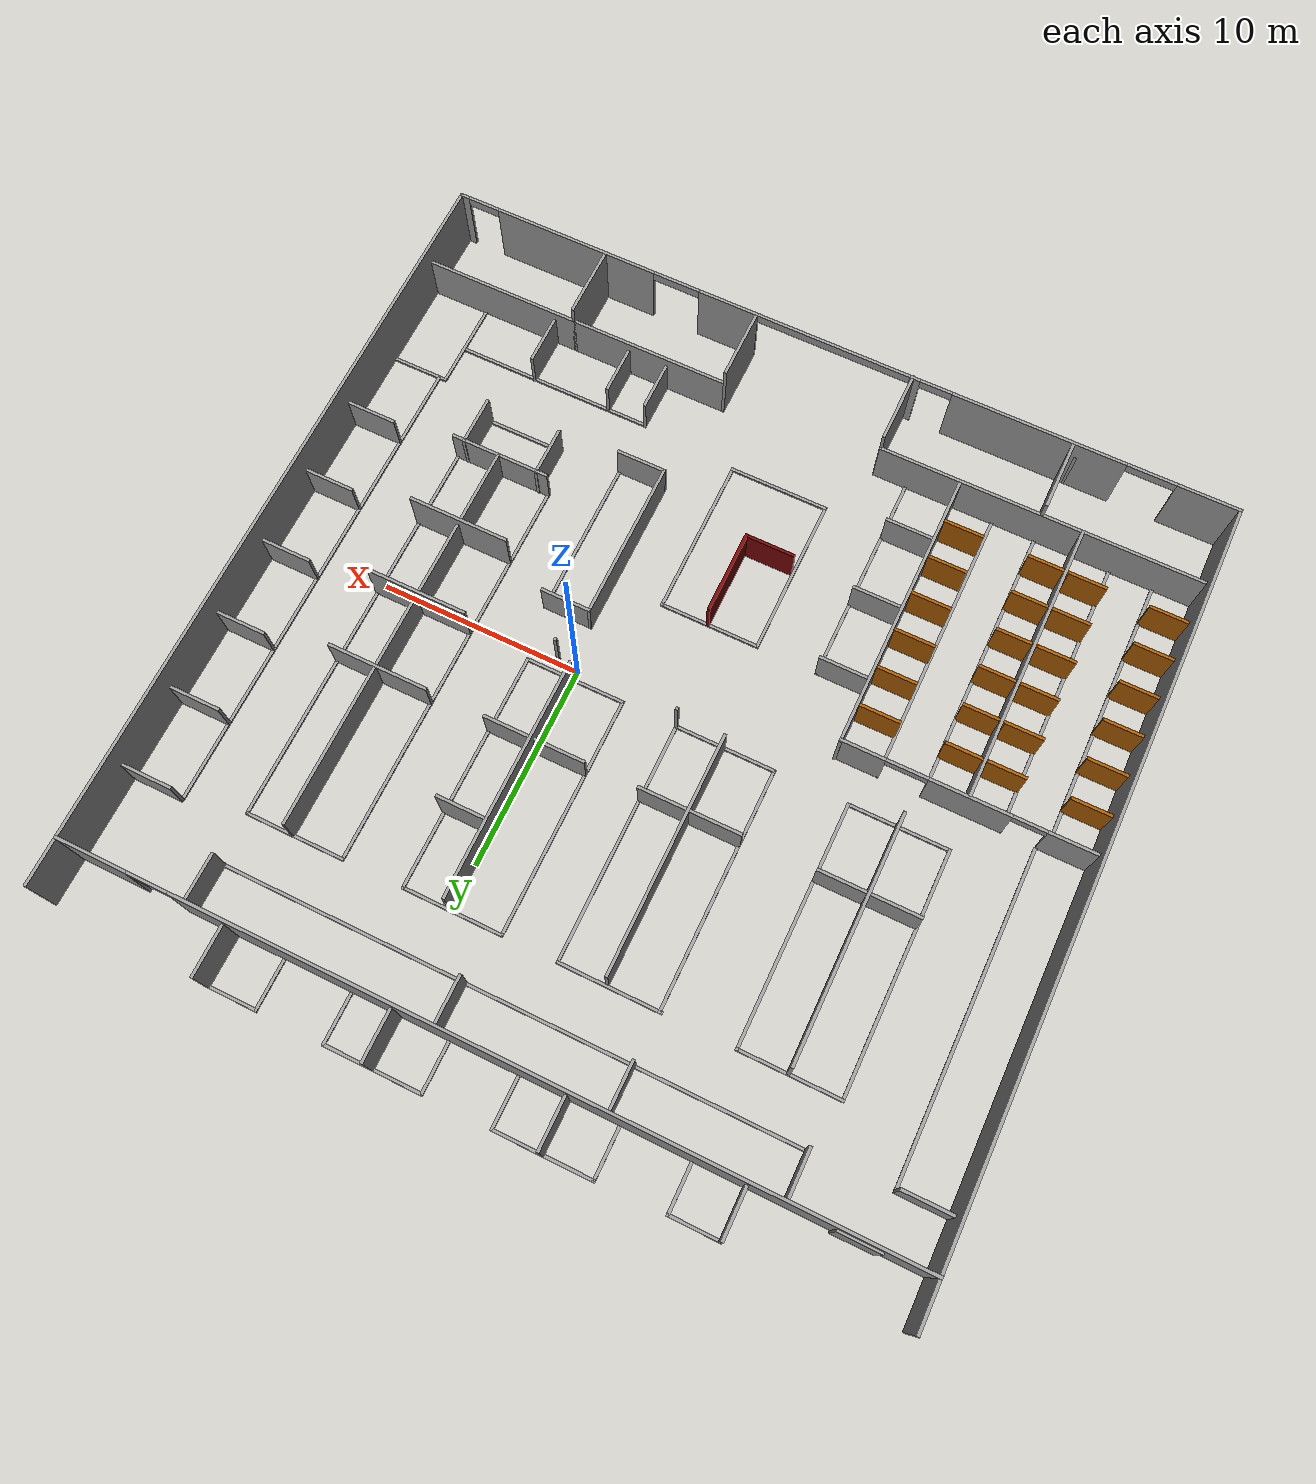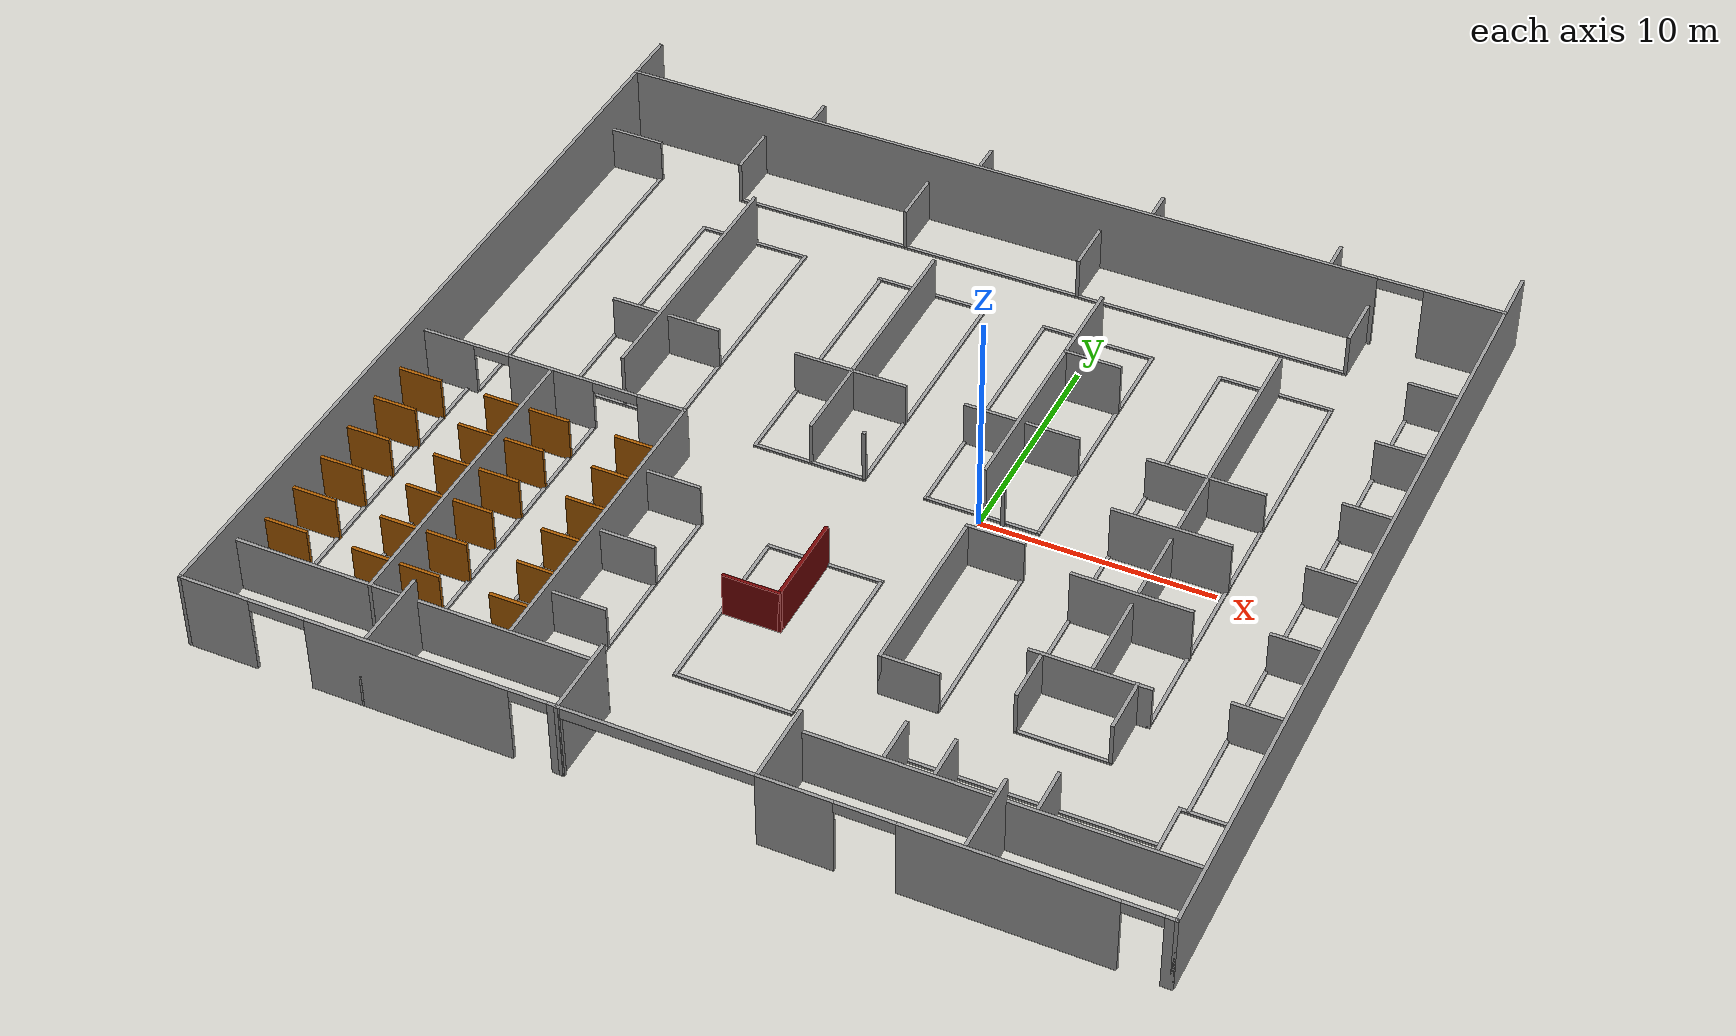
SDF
<?xml version='1.0'?>
<sdf version='1.7'>
  <model name='ATC_hall'>
    <pose>-4.287 0.374001 0 0 -0 0</pose>
    <link name='Door_8'>
      <collision name='Door_8_Collision'>
        <geometry>
          <box>
            <size>2 0.17 3</size>
          </box>
        </geometry>
        <pose>0 0 1.5 0 -0 0</pose>
      </collision>
      <visual name='Door_8_Visual'>
        <pose>0 0 1.5 0 -0 0</pose>
        <geometry>
          <box>
            <size>2 0.17 3</size>
          </box>
        </geometry>
        <material>
          <script>
            <uri>file://media/materials/scripts/gazebo.material</uri>
            <name>Gazebo/Grey</name>
          </script>
        </material>
      </visual>
      <pose>-16.713 16.852 0 0 -0 0</pose>
    </link>
    <link name='Wall_11'>
      <collision name='Wall_11_Collision'>
        <geometry>
          <box>
            <size>0.15 0.15 2.5</size>
          </box>
        </geometry>
        <pose>0 0 1.25 0 -0 0</pose>
      </collision>
      <visual name='Wall_11_Visual'>
        <pose>0 0 1.25 0 -0 0</pose>
        <geometry>
          <box>
            <size>0.15 0.15 2.5</size>
          </box>
        </geometry>
        <material>
          <script>
            <uri>file://media/materials/scripts/gazebo.material</uri>
            <name>Gazebo/Grey</name>
          </script>
          <ambient>1 1 1 1</ambient>
        </material>
        <meta>
          <layer>0</layer>
        </meta>
      </visual>
      <pose>-12.273 -19.224 0 0 -0 0</pose>
    </link>
    <link name='Wall_13'>
      <collision name='Wall_13_Collision'>
        <geometry>
          <box>
            <size>3.5 0.15 3.5</size>
          </box>
        </geometry>
        <pose>0 0 1.75 0 -0 0</pose>
      </collision>
      <visual name='Wall_13_Visual'>
        <pose>0 0 1.75 0 -0 0</pose>
        <geometry>
          <box>
            <size>3.5 0.15 3.5</size>
          </box>
        </geometry>
        <material>
          <script>
            <uri>file://media/materials/scripts/gazebo.material</uri>
            <name>Gazebo/Grey</name>
          </script>
          <ambient>0.890196 0.890196 0.890196 1</ambient>
        </material>
        <meta>
          <layer>0</layer>
        </meta>
      </visual>
      <pose>-11.92 -17.41 0 0 -0 1.5708</pose>
    </link>
    <link name='Wall_15'>
      <collision name='Wall_15_Collision'>
        <geometry>
          <box>
            <size>3.6 0.15 3.5</size>
          </box>
        </geometry>
        <pose>0 0 1.75 0 -0 0</pose>
      </collision>
      <visual name='Wall_15_Visual'>
        <pose>0 0 1.75 0 -0 0</pose>
        <geometry>
          <box>
            <size>3.6 0.15 3.5</size>
          </box>
        </geometry>
        <material>
          <script>
            <uri>file://media/materials/scripts/gazebo.material</uri>
            <name>Gazebo/Grey</name>
          </script>
          <ambient>0.890196 0.890196 0.890196 1</ambient>
        </material>
        <meta>
          <layer>0</layer>
        </meta>
      </visual>
      <pose>-3.92 -17.519 0 0 -0 -1.5708</pose>
    </link>
    <link name='Wall_17'>
      <collision name='Wall_17_Collision'>
        <geometry>
          <box>
            <size>3.5 0.15 3.5</size>
          </box>
        </geometry>
        <pose>0 0 1.75 0 -0 0</pose>
      </collision>
      <visual name='Wall_17_Visual'>
        <pose>0 0 1.75 0 -0 0</pose>
        <geometry>
          <box>
            <size>3.5 0.15 3.5</size>
          </box>
        </geometry>
        <material>
          <script>
            <uri>file://media/materials/scripts/gazebo.material</uri>
            <name>Gazebo/Grey</name>
          </script>
          <ambient>0.890196 0.890196 0.890196 1</ambient>
        </material>
        <meta>
          <layer>0</layer>
        </meta>
      </visual>
      <pose>4.08 -17.407 0 0 -0 1.5708</pose>
    </link>
    <link name='Wall_19'>
      <collision name='Wall_19_Collision'>
        <geometry>
          <box>
            <size>3.5 0.15 3.5</size>
          </box>
        </geometry>
        <pose>0 0 1.75 0 -0 0</pose>
      </collision>
      <visual name='Wall_19_Visual'>
        <pose>0 0 1.75 0 -0 0</pose>
        <geometry>
          <box>
            <size>3.5 0.15 3.5</size>
          </box>
        </geometry>
        <material>
          <script>
            <uri>file://media/materials/scripts/gazebo.material</uri>
            <name>Gazebo/Grey</name>
          </script>
          <ambient>0.890196 0.890196 0.890196 1</ambient>
        </material>
        <meta>
          <layer>0</layer>
        </meta>
      </visual>
      <pose>12.08 -17.407 0 0 -0 1.5708</pose>
    </link>
    <link name='Wall_195'>
      <collision name='Wall_195_Collision'>
        <geometry>
          <box>
            <size>2.5 0.15 2.5</size>
          </box>
        </geometry>
        <pose>0 0 1.25 0 -0 0</pose>
      </collision>
      <visual name='Wall_195_Visual'>
        <pose>0 0 1.25 0 -0 0</pose>
        <geometry>
          <box>
            <size>2.5 0.15 2.5</size>
          </box>
        </geometry>
        <material>
          <script>
            <uri>file://media/materials/scripts/gazebo.material</uri>
            <name>Gazebo/Grey</name>
          </script>
          <ambient>0 0 0 1</ambient>
        </material>
        <meta>
          <layer>0</layer>
        </meta>
      </visual>
      <pose>4.08 18.069 0 0 -0 1.5708</pose>
    </link>
    <link name='Wall_199'>
      <collision name='Wall_199_Collision'>
        <geometry>
          <box>
            <size>16.059 0.15 0.1</size>
          </box>
        </geometry>
        <pose>0 0 0.05 0 -0 0</pose>
      </collision>
      <visual name='Wall_199_Visual'>
        <pose>0 0 0.05 0 -0 0</pose>
        <geometry>
          <box>
            <size>16.059 0.15 0.1</size>
          </box>
        </geometry>
        <material>
          <script>
            <uri>file://media/materials/scripts/gazebo.material</uri>
            <name>Gazebo/Grey</name>
          </script>
          <ambient>0.454902 0.454902 0.454902 1</ambient>
        </material>
        <meta>
          <layer>0</layer>
        </meta>
      </visual>
      <pose>-17.5375 6.3535 0 0 -0 -1.57048</pose>
    </link>
    <link name='Wall_2'>
      <pose>0.004999 -19.224 0 0 -0 0</pose>
      <visual name='Wall_2_Visual_0'>
        <pose>-18.459 0 1.75 0 -0 0</pose>
        <geometry>
          <box>
            <size>3.082 0.15 3.5</size>
          </box>
        </geometry>
        <material>
          <script>
            <uri>file://media/materials/scripts/gazebo.material</uri>
            <name>Gazebo/Grey</name>
          </script>
          <ambient>0.890196 0.890196 0.890196 1</ambient>
        </material>
        <meta>
          <layer>0</layer>
        </meta>
      </visual>
      <collision name='Wall_2_Collision_0'>
        <geometry>
          <box>
            <size>3.082 0.15 3.5</size>
          </box>
        </geometry>
        <pose>-18.459 0 1.75 0 -0 0</pose>
      </collision>
      <visual name='Wall_2_Visual_1'>
        <pose>-10.213 0 1.75 0 -0 0</pose>
        <geometry>
          <box>
            <size>8.61 0.15 3.5</size>
          </box>
        </geometry>
        <material>
          <script>
            <uri>file://media/materials/scripts/gazebo.material</uri>
            <name>Gazebo/Grey</name>
          </script>
          <ambient>0.890196 0.890196 0.890196 1</ambient>
        </material>
        <meta>
          <layer>0</layer>
        </meta>
      </visual>
      <collision name='Wall_2_Collision_1'>
        <geometry>
          <box>
            <size>8.61 0.15 3.5</size>
          </box>
        </geometry>
        <pose>-10.213 0 1.75 0 -0 0</pose>
      </collision>
      <visual name='Wall_2_Visual_2'>
        <pose>-4.048 0 1.75 0 -0 0</pose>
        <geometry>
          <box>
            <size>0.519981 0.15 3.5</size>
          </box>
        </geometry>
        <material>
          <script>
            <uri>file://media/materials/scripts/gazebo.material</uri>
            <name>Gazebo/Grey</name>
          </script>
          <ambient>0.890196 0.890196 0.890196 1</ambient>
        </material>
        <meta>
          <layer>0</layer>
        </meta>
      </visual>
      <collision name='Wall_2_Collision_2'>
        <geometry>
          <box>
            <size>0.519981 0.15 3.5</size>
          </box>
        </geometry>
        <pose>-4.048 0 1.75 0 -0 0</pose>
      </collision>
      <visual name='Wall_2_Visual_3'>
        <pose>5.54699 0 1.75 0 -0 0</pose>
        <geometry>
          <box>
            <size>3.07002 0.15 3.5</size>
          </box>
        </geometry>
        <material>
          <script>
            <uri>file://media/materials/scripts/gazebo.material</uri>
            <name>Gazebo/Grey</name>
          </script>
          <ambient>0.890196 0.890196 0.890196 1</ambient>
        </material>
        <meta>
          <layer>0</layer>
        </meta>
      </visual>
      <collision name='Wall_2_Collision_3'>
        <geometry>
          <box>
            <size>3.07002 0.15 3.5</size>
          </box>
        </geometry>
        <pose>5.54699 0 1.75 0 -0 0</pose>
      </collision>
      <visual name='Wall_2_Visual_4'>
        <pose>13.6861 0 1.75 0 -0 0</pose>
        <geometry>
          <box>
            <size>8.40819 0.15 3.5</size>
          </box>
        </geometry>
        <material>
          <script>
            <uri>file://media/materials/scripts/gazebo.material</uri>
            <name>Gazebo/Grey</name>
          </script>
          <ambient>0.890196 0.890196 0.890196 1</ambient>
        </material>
        <meta>
          <layer>0</layer>
        </meta>
      </visual>
      <collision name='Wall_2_Collision_4'>
        <geometry>
          <box>
            <size>8.40819 0.15 3.5</size>
          </box>
        </geometry>
        <pose>13.6861 0 1.75 0 -0 0</pose>
      </collision>
      <visual name='Wall_2_Visual_5'>
        <pose>19.7451 0 1.75 0 -0 0</pose>
        <geometry>
          <box>
            <size>0.509814 0.15 3.5</size>
          </box>
        </geometry>
        <material>
          <script>
            <uri>file://media/materials/scripts/gazebo.material</uri>
            <name>Gazebo/Grey</name>
          </script>
          <ambient>0.890196 0.890196 0.890196 1</ambient>
        </material>
        <meta>
          <layer>0</layer>
        </meta>
      </visual>
      <collision name='Wall_2_Collision_5'>
        <geometry>
          <box>
            <size>0.509814 0.15 3.5</size>
          </box>
        </geometry>
        <pose>19.7451 0 1.75 0 -0 0</pose>
      </collision>
      <visual name='Wall_2_Visual_6'>
        <pose>-15.718 0 3.25 0 -0 0</pose>
        <geometry>
          <box>
            <size>2.4 0.15 0.5</size>
          </box>
        </geometry>
        <material>
          <script>
            <uri>file://media/materials/scripts/gazebo.material</uri>
            <name>Gazebo/Grey</name>
          </script>
          <ambient>0.890196 0.890196 0.890196 1</ambient>
        </material>
        <meta>
          <layer>0</layer>
        </meta>
      </visual>
      <collision name='Wall_2_Collision_6'>
        <geometry>
          <box>
            <size>2.4 0.15 0.5</size>
          </box>
        </geometry>
        <pose>-15.718 0 3.25 0 -0 0</pose>
      </collision>
      <visual name='Wall_2_Visual_7'>
        <pose>-5.108 0 3.25 0 -0 0</pose>
        <geometry>
          <box>
            <size>1.6 0.15 0.5</size>
          </box>
        </geometry>
        <material>
          <script>
            <uri>file://media/materials/scripts/gazebo.material</uri>
            <name>Gazebo/Grey</name>
          </script>
          <ambient>0.890196 0.890196 0.890196 1</ambient>
        </material>
        <meta>
          <layer>0</layer>
        </meta>
      </visual>
      <collision name='Wall_2_Collision_7'>
        <geometry>
          <box>
            <size>1.6 0.15 0.5</size>
          </box>
        </geometry>
        <pose>-5.108 0 3.25 0 -0 0</pose>
      </collision>
      <visual name='Wall_2_Visual_8'>
        <pose>0.111985 0 3.25 0 -0 0</pose>
        <geometry>
          <box>
            <size>7.8 0.15 0.5</size>
          </box>
        </geometry>
        <material>
          <script>
            <uri>file://media/materials/scripts/gazebo.material</uri>
            <name>Gazebo/Grey</name>
          </script>
          <ambient>0.890196 0.890196 0.890196 1</ambient>
        </material>
        <meta>
          <layer>0</layer>
        </meta>
      </visual>
      <collision name='Wall_2_Collision_8'>
        <geometry>
          <box>
            <size>7.8 0.15 0.5</size>
          </box>
        </geometry>
        <pose>0.111985 0 3.25 0 -0 0</pose>
      </collision>
      <visual name='Wall_2_Visual_9'>
        <pose>8.282 0 3.25 0 -0 0</pose>
        <geometry>
          <box>
            <size>2.4 0.15 0.5</size>
          </box>
        </geometry>
        <material>
          <script>
            <uri>file://media/materials/scripts/gazebo.material</uri>
            <name>Gazebo/Grey</name>
          </script>
          <ambient>0.890196 0.890196 0.890196 1</ambient>
        </material>
        <meta>
          <layer>0</layer>
        </meta>
      </visual>
      <collision name='Wall_2_Collision_9'>
        <geometry>
          <box>
            <size>2.4 0.15 0.5</size>
          </box>
        </geometry>
        <pose>8.282 0 3.25 0 -0 0</pose>
      </collision>
      <visual name='Wall_2_Visual_10'>
        <pose>18.6902 0 3.25 0 -0 0</pose>
        <geometry>
          <box>
            <size>1.6 0.15 0.5</size>
          </box>
        </geometry>
        <material>
          <script>
            <uri>file://media/materials/scripts/gazebo.material</uri>
            <name>Gazebo/Grey</name>
          </script>
          <ambient>0.890196 0.890196 0.890196 1</ambient>
        </material>
        <meta>
          <layer>0</layer>
        </meta>
      </visual>
      <collision name='Wall_2_Collision_10'>
        <geometry>
          <box>
            <size>1.6 0.15 0.5</size>
          </box>
        </geometry>
        <pose>18.6902 0 3.25 0 -0 0</pose>
      </collision>
    </link>
    <link name='Wall_204'>
      <collision name='Wall_204_Collision'>
        <geometry>
          <box>
            <size>14 0.15 0.1</size>
          </box>
        </geometry>
        <pose>0 0 0.05 0 -0 0</pose>
      </collision>
      <visual name='Wall_204_Visual'>
        <pose>0 0 0.05 0 -0 0</pose>
        <geometry>
          <box>
            <size>14 0.15 0.1</size>
          </box>
        </geometry>
        <material>
          <script>
            <uri>file://media/materials/scripts/gazebo.material</uri>
            <name>Gazebo/Grey</name>
          </script>
          <ambient>0.462745 0.462745 0.462745 1</ambient>
        </material>
        <meta>
          <layer>0</layer>
        </meta>
      </visual>
      <pose>-18.002 -8.696 0 0 -0 -1.5708</pose>
    </link>
    <link name='Wall_206'>
      <collision name='Wall_206_Collision'>
        <geometry>
          <box>
            <size>14 0.15 0.1</size>
          </box>
        </geometry>
        <pose>0 0 0.05 0 -0 0</pose>
      </collision>
      <visual name='Wall_206_Visual'>
        <pose>0 0 0.05 0 -0 0</pose>
        <geometry>
          <box>
            <size>14 0.15 0.1</size>
          </box>
        </geometry>
        <material>
          <script>
            <uri>file://media/materials/scripts/gazebo.material</uri>
            <name>Gazebo/Grey</name>
          </script>
          <ambient>0.462745 0.462745 0.462745 1</ambient>
        </material>
        <meta>
          <layer>0</layer>
        </meta>
      </visual>
      <pose>-15.864 -8.685 0 0 -0 -1.5708</pose>
    </link>
    <link name='Wall_208'>
      <collision name='Wall_208_Collision'>
        <geometry>
          <box>
            <size>14 0.15 0.1</size>
          </box>
        </geometry>
        <pose>0 0 0.05 0 -0 0</pose>
      </collision>
      <visual name='Wall_208_Visual'>
        <pose>0 0 0.05 0 -0 0</pose>
        <geometry>
          <box>
            <size>14 0.15 0.1</size>
          </box>
        </geometry>
        <material>
          <script>
            <uri>file://media/materials/scripts/gazebo.material</uri>
            <name>Gazebo/Grey</name>
          </script>
          <ambient>0.462745 0.462745 0.462745 1</ambient>
        </material>
        <meta>
          <layer>0</layer>
        </meta>
      </visual>
      <pose>-12.133 -8.708 0 0 -0 -1.5708</pose>
    </link>
    <link name='Wall_21'>
      <collision name='Wall_21_Collision'>
        <geometry>
          <box>
            <size>16.1 0.15 2.5</size>
          </box>
        </geometry>
        <pose>0 0 1.25 0 -0 0</pose>
      </collision>
      <visual name='Wall_21_Visual'>
        <pose>0 0 1.25 0 -0 0</pose>
        <geometry>
          <box>
            <size>16.1 0.15 2.5</size>
          </box>
        </geometry>
        <material>
          <script>
            <uri>file://media/materials/scripts/gazebo.material</uri>
            <name>Gazebo/Grey</name>
          </script>
          <ambient>0.890196 0.890196 0.890196 1</ambient>
        </material>
        <meta>
          <layer>0</layer>
        </meta>
      </visual>
      <pose>-11.934 -15.713 0 0 -0 0</pose>
    </link>
    <link name='Wall_211'>
      <collision name='Wall_211_Collision'>
        <geometry>
          <box>
            <size>14 0.15 0.1</size>
          </box>
        </geometry>
        <pose>0 0 0.05 0 -0 0</pose>
      </collision>
      <visual name='Wall_211_Visual'>
        <pose>0 0 0.05 0 -0 0</pose>
        <geometry>
          <box>
            <size>14 0.15 0.1</size>
          </box>
        </geometry>
        <material>
          <script>
            <uri>file://media/materials/scripts/gazebo.material</uri>
            <name>Gazebo/Grey</name>
          </script>
          <ambient>0.462745 0.462745 0.462745 1</ambient>
        </material>
        <meta>
          <layer>0</layer>
        </meta>
      </visual>
      <pose>-9.981 -8.67 0 0 -0 -1.5708</pose>
    </link>
    <link name='Wall_213'>
      <collision name='Wall_213_Collision'>
        <geometry>
          <box>
            <size>2.5 0.15 0.1</size>
          </box>
        </geometry>
        <pose>0 0 0.05 0 -0 0</pose>
      </collision>
      <visual name='Wall_213_Visual'>
        <pose>0 0 0.05 0 -0 0</pose>
        <geometry>
          <box>
            <size>2.5 0.15 0.1</size>
          </box>
        </geometry>
        <material>
          <script>
            <uri>file://media/materials/scripts/gazebo.material</uri>
            <name>Gazebo/Grey</name>
          </script>
          <ambient>0.454902 0.454902 0.454902 1</ambient>
        </material>
        <meta>
          <layer>0</layer>
        </meta>
      </visual>
      <pose>-10.745 19.117 0 0 -0 0</pose>
    </link>
    <link name='Wall_216'>
      <collision name='Wall_216_Collision'>
        <geometry>
          <box>
            <size>2.5 0.15 0.1</size>
          </box>
        </geometry>
        <pose>0 0 0.05 0 -0 0</pose>
      </collision>
      <visual name='Wall_216_Visual'>
        <pose>0 0 0.05 0 -0 0</pose>
        <geometry>
          <box>
            <size>2.5 0.15 0.1</size>
          </box>
        </geometry>
        <material>
          <script>
            <uri>file://media/materials/scripts/gazebo.material</uri>
            <name>Gazebo/Grey</name>
          </script>
          <ambient>0.454902 0.454902 0.454902 1</ambient>
        </material>
        <meta>
          <layer>0</layer>
        </meta>
      </visual>
      <pose>-9.57 17.942 0 0 -0 -1.5708</pose>
    </link>
    <link name='Wall_220'>
      <collision name='Wall_220_Collision'>
        <geometry>
          <box>
            <size>2.5 0.15 0.1</size>
          </box>
        </geometry>
        <pose>0 0 0.05 0 -0 0</pose>
      </collision>
      <visual name='Wall_220_Visual'>
        <pose>0 0 0.05 0 -0 0</pose>
        <geometry>
          <box>
            <size>2.5 0.15 0.1</size>
          </box>
        </geometry>
        <material>
          <script>
            <uri>file://media/materials/scripts/gazebo.material</uri>
            <name>Gazebo/Grey</name>
          </script>
          <ambient>0.462745 0.462745 0.462745 1</ambient>
        </material>
        <meta>
          <layer>0</layer>
        </meta>
      </visual>
      <pose>-5.095 19.238 0 0 -0 3.14159</pose>
    </link>
    <link name='Wall_222'>
      <collision name='Wall_222_Collision'>
        <geometry>
          <box>
            <size>2.5 0.15 0.1</size>
          </box>
        </geometry>
        <pose>0 0 0.05 0 -0 0</pose>
      </collision>
      <visual name='Wall_222_Visual'>
        <pose>0 0 0.05 0 -0 0</pose>
        <geometry>
          <box>
            <size>2.5 0.15 0.1</size>
          </box>
        </geometry>
        <material>
          <script>
            <uri>file://media/materials/scripts/gazebo.material</uri>
            <name>Gazebo/Grey</name>
          </script>
          <ambient>0.454902 0.454902 0.454902 1</ambient>
        </material>
        <meta>
          <layer>0</layer>
        </meta>
      </visual>
      <pose>-6.27 18.063 0 0 -0 -1.5708</pose>
    </link>
    <link name='Wall_224'>
      <collision name='Wall_224_Collision'>
        <geometry>
          <box>
            <size>2.5 0.15 0.1</size>
          </box>
        </geometry>
        <pose>0 0 0.05 0 -0 0</pose>
      </collision>
      <visual name='Wall_224_Visual'>
        <pose>0 0 0.05 0 -0 0</pose>
        <geometry>
          <box>
            <size>2.5 0.15 0.1</size>
          </box>
        </geometry>
        <material>
          <script>
            <uri>file://media/materials/scripts/gazebo.material</uri>
            <name>Gazebo/Grey</name>
          </script>
          <ambient>0.462745 0.462745 0.462745 1</ambient>
        </material>
        <meta>
          <layer>0</layer>
        </meta>
      </visual>
      <pose>-2.745 19.238 0 0 -0 0</pose>
    </link>
    <link name='Wall_226'>
      <collision name='Wall_226_Collision'>
        <geometry>
          <box>
            <size>2.5 0.15 0.1</size>
          </box>
        </geometry>
        <pose>0 0 0.05 0 -0 0</pose>
      </collision>
      <visual name='Wall_226_Visual'>
        <pose>0 0 0.05 0 -0 0</pose>
        <geometry>
          <box>
            <size>2.5 0.15 0.1</size>
          </box>
        </geometry>
        <material>
          <script>
            <uri>file://media/materials/scripts/gazebo.material</uri>
            <name>Gazebo/Grey</name>
          </script>
          <ambient>0.462745 0.462745 0.462745 1</ambient>
        </material>
        <meta>
          <layer>0</layer>
        </meta>
      </visual>
      <pose>-1.57 18.063 0 0 -0 -1.5708</pose>
    </link>
    <link name='Wall_228'>
      <collision name='Wall_228_Collision'>
        <geometry>
          <box>
            <size>2.5 0.15 0.1</size>
          </box>
        </geometry>
        <pose>0 0 0.05 0 -0 0</pose>
      </collision>
      <visual name='Wall_228_Visual'>
        <pose>0 0 0.05 0 -0 0</pose>
        <geometry>
          <box>
            <size>2.5 0.15 0.1</size>
          </box>
        </geometry>
        <material>
          <script>
            <uri>file://media/materials/scripts/gazebo.material</uri>
            <name>Gazebo/Grey</name>
          </script>
          <ambient>0.462745 0.462745 0.462745 1</ambient>
        </material>
        <meta>
          <layer>0</layer>
        </meta>
      </visual>
      <pose>2.905 19.244 0 0 -0 3.14159</pose>
    </link>
    <link name='Wall_23'>
      <collision name='Wall_23_Collision'>
        <geometry>
          <box>
            <size>16 0.15 2.5</size>
          </box>
        </geometry>
        <pose>0 0 1.25 0 -0 0</pose>
      </collision>
      <visual name='Wall_23_Visual'>
        <pose>0 0 1.25 0 -0 0</pose>
        <geometry>
          <box>
            <size>16 0.15 2.5</size>
          </box>
        </geometry>
        <material>
          <script>
            <uri>file://media/materials/scripts/gazebo.material</uri>
            <name>Gazebo/Grey</name>
          </script>
          <ambient>0.890196 0.890196 0.890196 1</ambient>
        </material>
        <meta>
          <layer>0</layer>
        </meta>
      </visual>
      <pose>12.005 -15.732 0 0 -0 0</pose>
    </link>
    <link name='Wall_230'>
      <collision name='Wall_230_Collision'>
        <geometry>
          <box>
            <size>2.5 0.15 0.1</size>
          </box>
        </geometry>
        <pose>0 0 0.05 0 -0 0</pose>
      </collision>
      <visual name='Wall_230_Visual'>
        <pose>0 0 0.05 0 -0 0</pose>
        <geometry>
          <box>
            <size>2.5 0.15 0.1</size>
          </box>
        </geometry>
        <material>
          <script>
            <uri>file://media/materials/scripts/gazebo.material</uri>
            <name>Gazebo/Grey</name>
          </script>
          <ambient>0.462745 0.462745 0.462745 1</ambient>
        </material>
        <meta>
          <layer>0</layer>
        </meta>
      </visual>
      <pose>1.73 18.069 0 0 -0 -1.5708</pose>
    </link>
    <link name='Wall_232'>
      <collision name='Wall_232_Collision'>
        <geometry>
          <box>
            <size>2.5 0.15 0.1</size>
          </box>
        </geometry>
        <pose>0 0 0.05 0 -0 0</pose>
      </collision>
      <visual name='Wall_232_Visual'>
        <pose>0 0 0.05 0 -0 0</pose>
        <geometry>
          <box>
            <size>2.5 0.15 0.1</size>
          </box>
        </geometry>
        <material>
          <script>
            <uri>file://media/materials/scripts/gazebo.material</uri>
            <name>Gazebo/Grey</name>
          </script>
          <ambient>0.454902 0.454902 0.454902 1</ambient>
        </material>
        <meta>
          <layer>0</layer>
        </meta>
      </visual>
      <pose>5.255 19.244 0 0 -0 0</pose>
    </link>
    <link name='Wall_234'>
      <collision name='Wall_234_Collision'>
        <geometry>
          <box>
            <size>2.5 0.15 0.1</size>
          </box>
        </geometry>
        <pose>0 0 0.05 0 -0 0</pose>
      </collision>
      <visual name='Wall_234_Visual'>
        <pose>0 0 0.05 0 -0 0</pose>
        <geometry>
          <box>
            <size>2.5 0.15 0.1</size>
          </box>
        </geometry>
        <material>
          <script>
            <uri>file://media/materials/scripts/gazebo.material</uri>
            <name>Gazebo/Grey</name>
          </script>
          <ambient>0.454902 0.454902 0.454902 1</ambient>
        </material>
        <meta>
          <layer>0</layer>
        </meta>
      </visual>
      <pose>6.43 18.069 0 0 -0 -1.5708</pose>
    </link>
    <link name='Wall_236'>
      <collision name='Wall_236_Collision'>
        <geometry>
          <box>
            <size>2.5 0.15 0.1</size>
          </box>
        </geometry>
        <pose>0 0 0.05 0 -0 0</pose>
      </collision>
      <visual name='Wall_236_Visual'>
        <pose>0 0 0.05 0 -0 0</pose>
        <geometry>
          <box>
            <size>2.5 0.15 0.1</size>
          </box>
        </geometry>
        <material>
          <script>
            <uri>file://media/materials/scripts/gazebo.material</uri>
            <name>Gazebo/Grey</name>
          </script>
          <ambient>0.454902 0.454902 0.454902 1</ambient>
        </material>
        <meta>
          <layer>0</layer>
        </meta>
      </visual>
      <pose>10.905 19.238 0 0 -0 3.14159</pose>
    </link>
    <link name='Wall_238'>
      <collision name='Wall_238_Collision'>
        <geometry>
          <box>
            <size>2.5 0.15 0.1</size>
          </box>
        </geometry>
        <pose>0 0 0.05 0 -0 0</pose>
      </collision>
      <visual name='Wall_238_Visual'>
        <pose>0 0 0.05 0 -0 0</pose>
        <geometry>
          <box>
            <size>2.5 0.15 0.1</size>
          </box>
        </geometry>
        <material>
          <script>
            <uri>file://media/materials/scripts/gazebo.material</uri>
            <name>Gazebo/Grey</name>
          </script>
          <ambient>0.454902 0.454902 0.454902 1</ambient>
        </material>
        <meta>
          <layer>0</layer>
        </meta>
      </visual>
      <pose>9.73 18.063 0 0 -0 -1.5708</pose>
    </link>
    <link name='Wall_25'>
      <collision name='Wall_25_Collision'>
        <geometry>
          <box>
            <size>14.0341 0.15 2.5</size>
          </box>
        </geometry>
        <pose>0 0 1.25 0 -0 0</pose>
      </collision>
      <visual name='Wall_25_Visual'>
        <pose>0 0 1.25 0 -0 0</pose>
        <geometry>
          <box>
            <size>14.0341 0.15 2.5</size>
          </box>
        </geometry>
        <material>
          <script>
            <uri>file://media/materials/scripts/gazebo.material</uri>
            <name>Gazebo/Grey</name>
          </script>
          <ambient>0.890196 0.890196 0.890196 1</ambient>
        </material>
        <meta>
          <layer>0</layer>
        </meta>
      </visual>
      <pose>-7.92273 -8.65395 0 0 -0 1.57119</pose>
    </link>
    <link name='Wall_27'>
      <pose>-13.8505 -1.75145 0 0 -0 3.14159</pose>
      <visual name='Wall_27_Visual_0'>
        <pose>-4.90273 0 1.25 0 -0 0</pose>
        <geometry>
          <box>
            <size>2.19455 0.15 2.5</size>
          </box>
        </geometry>
        <material>
          <script>
            <uri>file://media/materials/scripts/gazebo.material</uri>
            <name>Gazebo/Grey</name>
          </script>
          <ambient>0.890196 0.890196 0.890196 1</ambient>
        </material>
        <meta>
          <layer>0</layer>
        </meta>
      </visual>
      <collision name='Wall_27_Collision_0'>
        <geometry>
          <box>
            <size>2.19455 0.15 2.5</size>
          </box>
        </geometry>
        <pose>-4.90273 0 1.25 0 -0 0</pose>
      </collision>
      <visual name='Wall_27_Visual_1'>
        <pose>0.128549 0 1.25 0 -0 0</pose>
        <geometry>
          <box>
            <size>3.868 0.15 2.5</size>
          </box>
        </geometry>
        <material>
          <script>
            <uri>file://media/materials/scripts/gazebo.material</uri>
            <name>Gazebo/Grey</name>
          </script>
          <ambient>0.890196 0.890196 0.890196 1</ambient>
        </material>
        <meta>
          <layer>0</layer>
        </meta>
      </visual>
      <collision name='Wall_27_Collision_1'>
        <geometry>
          <box>
            <size>3.868 0.15 2.5</size>
          </box>
        </geometry>
        <pose>0.128549 0 1.25 0 -0 0</pose>
      </collision>
      <visual name='Wall_27_Visual_2'>
        <pose>4.83127 0 1.25 0 -0 0</pose>
        <geometry>
          <box>
            <size>2.33745 0.15 2.5</size>
          </box>
        </geometry>
        <material>
          <script>
            <uri>file://media/materials/scripts/gazebo.material</uri>
            <name>Gazebo/Grey</name>
          </script>
          <ambient>0.890196 0.890196 0.890196 1</ambient>
        </material>
        <meta>
          <layer>0</layer>
        </meta>
      </visual>
      <collision name='Wall_27_Collision_2'>
        <geometry>
          <box>
            <size>2.33745 0.15 2.5</size>
          </box>
        </geometry>
        <pose>4.83127 0 1.25 0 -0 0</pose>
      </collision>
      <visual name='Wall_27_Visual_3'>
        <pose>-2.80545 0 2.25 0 -0 0</pose>
        <geometry>
          <box>
            <size>2 0.15 0.5</size>
          </box>
        </geometry>
        <material>
          <script>
            <uri>file://media/materials/scripts/gazebo.material</uri>
            <name>Gazebo/Grey</name>
          </script>
          <ambient>0.890196 0.890196 0.890196 1</ambient>
        </material>
        <meta>
          <layer>0</layer>
        </meta>
      </visual>
      <collision name='Wall_27_Collision_3'>
        <geometry>
          <box>
            <size>2 0.15 0.5</size>
          </box>
        </geometry>
        <pose>-2.80545 0 2.25 0 -0 0</pose>
      </collision>
      <visual name='Wall_27_Visual_4'>
        <pose>2.86255 0 2.25 0 -0 0</pose>
        <geometry>
          <box>
            <size>1.6 0.15 0.5</size>
          </box>
        </geometry>
        <material>
          <script>
            <uri>file://media/materials/scripts/gazebo.material</uri>
            <name>Gazebo/Grey</name>
          </script>
          <ambient>0.890196 0.890196 0.890196 1</ambient>
        </material>
        <meta>
          <layer>0</layer>
        </meta>
      </visual>
      <collision name='Wall_27_Collision_4'>
        <geometry>
          <box>
            <size>1.6 0.15 0.5</size>
          </box>
        </geometry>
        <pose>2.86255 0 2.25 0 -0 0</pose>
      </collision>
    </link>
    <link name='Wall_29'>
      <collision name='Wall_29_Collision'>
        <geometry>
          <box>
            <size>14 0.15 2.5</size>
          </box>
        </geometry>
        <pose>0 0 1.25 0 -0 0</pose>
      </collision>
      <visual name='Wall_29_Visual'>
        <pose>0 0 1.25 0 -0 0</pose>
        <geometry>
          <box>
            <size>14 0.15 2.5</size>
          </box>
        </geometry>
        <material>
          <script>
            <uri>file://media/materials/scripts/gazebo.material</uri>
            <name>Gazebo/Grey</name>
          </script>
          <ambient>0.890196 0.890196 0.890196 1</ambient>
        </material>
        <meta>
          <layer>0</layer>
        </meta>
      </visual>
      <pose>-13.92 -8.791 0 0 -0 1.5708</pose>
    </link>
    <link name='Wall_306'>
      <collision name='Wall_306_Collision'>
        <geometry>
          <box>
            <size>2.5 0.15 2</size>
          </box>
        </geometry>
        <pose>0 0 1 0 -0 0</pose>
      </collision>
      <visual name='Wall_306_Visual'>
        <pose>0 0 1 0 -0 0</pose>
        <geometry>
          <box>
            <size>2.5 0.15 2</size>
          </box>
        </geometry>
        <material>
          <script>
            <uri>file://media/materials/scripts/gazebo.material</uri>
            <name>Gazebo/Grey</name>
          </script>
          <ambient>0 0 0 1</ambient>
        </material>
        <meta>
          <layer>0</layer>
        </meta>
      </visual>
      <pose>-13.62 15.573 0 0 -0 -1.5708</pose>
    </link>
    <link name='Wall_308'>
      <collision name='Wall_308_Collision'>
        <geometry>
          <box>
            <size>28 0.15 0.1</size>
          </box>
        </geometry>
        <pose>0 0 0.05 0 -0 0</pose>
      </collision>
      <visual name='Wall_308_Visual'>
        <pose>0 0 0.05 0 -0 0</pose>
        <geometry>
          <box>
            <size>28 0.15 0.1</size>
          </box>
        </geometry>
        <material>
          <script>
            <uri>file://media/materials/scripts/gazebo.material</uri>
            <name>Gazebo/Grey</name>
          </script>
          <ambient>0.454902 0.454902 0.454902 1</ambient>
        </material>
        <meta>
          <layer>0</layer>
        </meta>
      </visual>
      <pose>0.304999 14.394 0 0 -0 -0.000287</pose>
    </link>
    <link name='Wall_310'>
      <collision name='Wall_310_Collision'>
        <geometry>
          <box>
            <size>2.5 0.15 2</size>
          </box>
        </geometry>
        <pose>0 0 1 0 -0 0</pose>
      </collision>
      <visual name='Wall_310_Visual'>
        <pose>0 0 1 0 -0 0</pose>
        <geometry>
          <box>
            <size>2.5 0.15 2</size>
          </box>
        </geometry>
        <material>
          <script>
            <uri>file://media/materials/scripts/gazebo.material</uri>
            <name>Gazebo/Grey</name>
          </script>
          <ambient>0 0 0 1</ambient>
        </material>
        <meta>
          <layer>0</layer>
        </meta>
      </visual>
      <pose>-5.735 15.573 0 0 -0 -1.5708</pose>
    </link>
    <link name='Wall_314'>
      <collision name='Wall_314_Collision'>
        <geometry>
          <box>
            <size>2.5 0.15 2</size>
          </box>
        </geometry>
        <pose>0 0 1 0 -0 0</pose>
      </collision>
      <visual name='Wall_314_Visual'>
        <pose>0 0 1 0 -0 0</pose>
        <geometry>
          <box>
            <size>2.5 0.15 2</size>
          </box>
        </geometry>
        <material>
          <script>
            <uri>file://media/materials/scripts/gazebo.material</uri>
            <name>Gazebo/Grey</name>
          </script>
          <ambient>0 0 0 1</ambient>
        </material>
        <meta>
          <layer>0</layer>
        </meta>
      </visual>
      <pose>2.263 15.573 0 0 -0 -1.5708</pose>
    </link>
    <link name='Wall_323'>
      <collision name='Wall_323_Collision'>
        <geometry>
          <box>
            <size>2.5 0.15 2</size>
          </box>
        </geometry>
        <pose>0 0 1 0 -0 0</pose>
      </collision>
      <visual name='Wall_323_Visual'>
        <pose>0 0 1 0 -0 0</pose>
        <geometry>
          <box>
            <size>2.5 0.15 2</size>
          </box>
        </geometry>
        <material>
          <script>
            <uri>file://media/materials/scripts/gazebo.material</uri>
            <name>Gazebo/Grey</name>
          </script>
          <ambient>0 0 0 1</ambient>
        </material>
        <meta>
          <layer>0</layer>
        </meta>
      </visual>
      <pose>14.237 15.565 0 0 -0 -1.57675</pose>
    </link>
    <link name='Wall_325'>
      <collision name='Wall_325_Collision'>
        <geometry>
          <box>
            <size>0.15 0.15 0.1</size>
          </box>
        </geometry>
        <pose>0 0 0.05 0 -0 0</pose>
      </collision>
      <visual name='Wall_325_Visual'>
        <pose>0 0 0.05 0 -0 0</pose>
        <geometry>
          <box>
            <size>0.15 0.15 0.1</size>
          </box>
        </geometry>
        <material>
          <script>
            <uri>file://media/materials/scripts/gazebo.material</uri>
            <name>Gazebo/Grey</name>
          </script>
          <ambient>1 1 1 1</ambient>
        </material>
        <meta>
          <layer>0</layer>
        </meta>
      </visual>
      <pose>-5.803 11.898 0 0 -0 0</pose>
    </link>
    <link name='Wall_327'>
      <collision name='Wall_327_Collision'>
        <geometry>
          <box>
            <size>12 0.15 0.1</size>
          </box>
        </geometry>
        <pose>0 0 0.05 0 -0 0</pose>
      </collision>
      <visual name='Wall_327_Visual'>
        <pose>0 0 0.05 0 -0 0</pose>
        <geometry>
          <box>
            <size>12 0.15 0.1</size>
          </box>
        </geometry>
        <material>
          <script>
            <uri>file://media/materials/scripts/gazebo.material</uri>
            <name>Gazebo/Grey</name>
          </script>
          <ambient>0.454902 0.454902 0.454902 1</ambient>
        </material>
        <meta>
          <layer>0</layer>
        </meta>
      </visual>
      <pose>-5.735 5.973 0 0 -0 -1.5708</pose>
    </link>
    <link name='Wall_329'>
      <collision name='Wall_329_Collision'>
        <geometry>
          <box>
            <size>5 0.15 0.1</size>
          </box>
        </geometry>
        <pose>0 0 0.05 0 -0 0</pose>
      </collision>
      <visual name='Wall_329_Visual'>
        <pose>0 0 0.05 0 -0 0</pose>
        <geometry>
          <box>
            <size>5 0.15 0.1</size>
          </box>
        </geometry>
        <material>
          <script>
            <uri>file://media/materials/scripts/gazebo.material</uri>
            <name>Gazebo/Grey</name>
          </script>
          <ambient>0.454902 0.454902 0.454902 1</ambient>
        </material>
        <meta>
          <layer>0</layer>
        </meta>
      </visual>
      <pose>-3.31 11.893 0 0 -0 -0.002062</pose>
    </link>
    <link name='Wall_33'>
      <collision name='Wall_33_Collision'>
        <geometry>
          <box>
            <size>2 0.15 2</size>
          </box>
        </geometry>
        <pose>0 0 1 0 -0 0</pose>
      </collision>
      <visual name='Wall_33_Visual'>
        <pose>0 0 1 0 -0 0</pose>
        <geometry>
          <box>
            <size>2 0.15 2</size>
          </box>
        </geometry>
        <material>
          <script>
            <uri>file://media/materials/scripts/gazebo.material</uri>
            <name>Gazebo/Grey</name>
          </script>
          <ambient>0.666667 0.356863 0 1</ambient>
        </material>
        <meta>
          <layer>0</layer>
        </meta>
      </visual>
      <pose>-18.965 -13.791 0 0 -0 0</pose>
    </link>
    <link name='Wall_331'>
      <collision name='Wall_331_Collision'>
        <geometry>
          <box>
            <size>12 0.15 0.1</size>
          </box>
        </geometry>
        <pose>0 0 0.05 0 -0 0</pose>
      </collision>
      <visual name='Wall_331_Visual'>
        <pose>0 0 0.05 0 -0 0</pose>
        <geometry>
          <box>
            <size>12 0.15 0.1</size>
          </box>
        </geometry>
        <material>
          <script>
            <uri>file://media/materials/scripts/gazebo.material</uri>
            <name>Gazebo/Grey</name>
          </script>
          <ambient>0.454902 0.454902 0.454902 1</ambient>
        </material>
        <meta>
          <layer>0</layer>
        </meta>
      </visual>
      <pose>-0.885001 5.963 0 0 -0 -1.5708</pose>
    </link>
    <link name='Wall_332'>
      <collision name='Wall_332_Collision'>
        <geometry>
          <box>
            <size>0.15 0.15 2.5</size>
          </box>
        </geometry>
        <pose>0 0 1.25 0 -0 0</pose>
      </collision>
      <visual name='Wall_332_Visual'>
        <pose>0 0 1.25 0 -0 0</pose>
        <geometry>
          <box>
            <size>0.15 0.15 2.5</size>
          </box>
        </geometry>
        <material>
          <script>
            <uri>file://media/materials/scripts/gazebo.material</uri>
            <name>Gazebo/Grey</name>
          </script>
          <ambient>1 1 1 1</ambient>
        </material>
        <meta>
          <layer>0</layer>
        </meta>
      </visual>
      <pose>-0.885001 0.037999 0 0 -0 0</pose>
    </link>
    <link name='Wall_334'>
      <collision name='Wall_334_Collision'>
        <geometry>
          <box>
            <size>5 0.15 0.1</size>
          </box>
        </geometry>
        <pose>0 0 0.05 0 -0 0</pose>
      </collision>
      <visual name='Wall_334_Visual'>
        <pose>0 0 0.05 0 -0 0</pose>
        <geometry>
          <box>
            <size>5 0.15 0.1</size>
          </box>
        </geometry>
        <material>
          <script>
            <uri>file://media/materials/scripts/gazebo.material</uri>
            <name>Gazebo/Grey</name>
          </script>
          <ambient>0.454902 0.454902 0.454902 1</ambient>
        </material>
        <meta>
          <layer>0</layer>
        </meta>
      </visual>
      <pose>-3.31 0.042999 0 0 -0 3.13953</pose>
    </link>
    <link name='Wall_336'>
      <collision name='Wall_336_Collision'>
        <geometry>
          <box>
            <size>11.8 0.15 2</size>
          </box>
        </geometry>
        <pose>0 0 1 0 -0 0</pose>
      </collision>
      <visual name='Wall_336_Visual'>
        <pose>0 0 1 0 -0 0</pose>
        <geometry>
          <box>
            <size>11.8 0.15 2</size>
          </box>
        </geometry>
        <material>
          <script>
            <uri>file://media/materials/scripts/gazebo.material</uri>
            <name>Gazebo/Grey</name>
          </script>
          <ambient>0 0 0 1</ambient>
        </material>
        <meta>
          <layer>0</layer>
        </meta>
      </visual>
      <pose>-3.235 5.932 0 0 -0 -1.5708</pose>
    </link>
    <link name='Wall_338'>
      <collision name='Wall_338_Collision'>
        <geometry>
          <box>
            <size>5 0.15 2</size>
          </box>
        </geometry>
        <pose>0 0 1 0 -0 0</pose>
      </collision>
      <visual name='Wall_338_Visual'>
        <pose>0 0 1 0 -0 0</pose>
        <geometry>
          <box>
            <size>5 0.15 2</size>
          </box>
        </geometry>
        <material>
          <script>
            <uri>file://media/materials/scripts/gazebo.material</uri>
            <name>Gazebo/Grey</name>
          </script>
          <ambient>0 0 0 1</ambient>
        </material>
        <meta>
          <layer>0</layer>
        </meta>
      </visual>
      <pose>-3.31 3.848 0 0 -0 0</pose>
    </link>
    <link name='Wall_340'>
      <collision name='Wall_340_Collision'>
        <geometry>
          <box>
            <size>12 0.15 0.1</size>
          </box>
        </geometry>
        <pose>0 0 0.05 0 -0 0</pose>
      </collision>
      <visual name='Wall_340_Visual'>
        <pose>0 0 0.05 0 -0 0</pose>
        <geometry>
          <box>
            <size>12 0.15 0.1</size>
          </box>
        </geometry>
        <material>
          <script>
            <uri>file://media/materials/scripts/gazebo.material</uri>
            <name>Gazebo/Grey</name>
          </script>
          <ambient>0.454902 0.454902 0.454902 1</ambient>
        </material>
        <meta>
          <layer>0</layer>
        </meta>
      </visual>
      <pose>-9.335 5.973 0 0 -0 -1.5708</pose>
    </link>
    <link name='Wall_343'>
      <collision name='Wall_343_Collision'>
        <geometry>
          <box>
            <size>5 0.15 0.1</size>
          </box>
        </geometry>
        <pose>0 0 0.05 0 -0 0</pose>
      </collision>
      <visual name='Wall_343_Visual'>
        <pose>0 0 0.05 0 -0 0</pose>
        <geometry>
          <box>
            <size>5 0.15 0.1</size>
          </box>
        </geometry>
        <material>
          <script>
            <uri>file://media/materials/scripts/gazebo.material</uri>
            <name>Gazebo/Grey</name>
          </script>
          <ambient>0.454902 0.454902 0.454902 1</ambient>
        </material>
        <meta>
          <layer>0</layer>
        </meta>
      </visual>
      <pose>-11.76 11.898 0 0 -0 3.14159</pose>
    </link>
    <link name='Wall_345'>
      <collision name='Wall_345_Collision'>
        <geometry>
          <box>
            <size>12 0.15 0.1</size>
          </box>
        </geometry>
        <pose>0 0 0.05 0 -0 0</pose>
      </collision>
      <visual name='Wall_345_Visual'>
        <pose>0 0 0.05 0 -0 0</pose>
        <geometry>
          <box>
            <size>12 0.15 0.1</size>
          </box>
        </geometry>
        <material>
          <script>
            <uri>file://media/materials/scripts/gazebo.material</uri>
            <name>Gazebo/Grey</name>
          </script>
          <ambient>0.454902 0.454902 0.454902 1</ambient>
        </material>
        <meta>
          <layer>0</layer>
        </meta>
      </visual>
      <pose>-14.185 5.973 0 0 -0 -1.5708</pose>
    </link>
    <link name='Wall_347'>
      <collision name='Wall_347_Collision'>
        <geometry>
          <box>
            <size>5 0.15 0.1</size>
          </box>
        </geometry>
        <pose>0 0 0.05 0 -0 0</pose>
      </collision>
      <visual name='Wall_347_Visual'>
        <pose>0 0 0.05 0 -0 0</pose>
        <geometry>
          <box>
            <size>5 0.15 0.1</size>
          </box>
        </geometry>
        <material>
          <script>
            <uri>file://media/materials/scripts/gazebo.material</uri>
            <name>Gazebo/Grey</name>
          </script>
          <ambient>0.454902 0.454902 0.454902 1</ambient>
        </material>
        <meta>
          <layer>0</layer>
        </meta>
      </visual>
      <pose>-11.76 0.047999 0 0 -0 0</pose>
    </link>
    <link name='Wall_349'>
      <collision name='Wall_349_Collision'>
        <geometry>
          <box>
            <size>4.9 0.15 2</size>
          </box>
        </geometry>
        <pose>0 0 1 0 -0 0</pose>
      </collision>
      <visual name='Wall_349_Visual'>
        <pose>0 0 1 0 -0 0</pose>
        <geometry>
          <box>
            <size>4.9 0.15 2</size>
          </box>
        </geometry>
        <material>
          <script>
            <uri>file://media/materials/scripts/gazebo.material</uri>
            <name>Gazebo/Grey</name>
          </script>
          <ambient>0 0 0 1</ambient>
        </material>
        <meta>
          <layer>0</layer>
        </meta>
      </visual>
      <pose>-11.726 3.848 0 0 -0 3.14159</pose>
    </link>
    <link name='Wall_352'>
      <collision name='Wall_352_Collision'>
        <geometry>
          <box>
            <size>11.9 0.15 2.5</size>
          </box>
        </geometry>
        <pose>0 0 1.25 0 -0 0</pose>
      </collision>
      <visual name='Wall_352_Visual'>
        <pose>0 0 1.25 0 -0 0</pose>
        <geometry>
          <box>
            <size>11.9 0.15 2.5</size>
          </box>
        </geometry>
        <material>
          <script>
            <uri>file://media/materials/scripts/gazebo.material</uri>
            <name>Gazebo/Grey</name>
          </script>
          <ambient>0 0 0 1</ambient>
        </material>
        <meta>
          <layer>0</layer>
        </meta>
      </visual>
      <pose>-11.685 5.992 0 0 -0 -1.5708</pose>
    </link>
    <link name='Wall_354'>
      <collision name='Wall_354_Collision'>
        <geometry>
          <box>
            <size>12 0.15 0.1</size>
          </box>
        </geometry>
        <pose>0 0 0.05 0 -0 0</pose>
      </collision>
      <visual name='Wall_354_Visual'>
        <pose>0 0 0.05 0 -0 0</pose>
        <geometry>
          <box>
            <size>12 0.15 0.1</size>
          </box>
        </geometry>
        <material>
          <script>
            <uri>file://media/materials/scripts/gazebo.material</uri>
            <name>Gazebo/Grey</name>
          </script>
          <ambient>0.454902 0.454902 0.454902 1</ambient>
        </material>
        <meta>
          <layer>0</layer>
        </meta>
      </visual>
      <pose>1.815 5.963 0 0 -0 -1.5708</pose>
    </link>
    <link name='Wall_358'>
      <collision name='Wall_358_Collision'>
        <geometry>
          <box>
            <size>5 0.15 0.1</size>
          </box>
        </geometry>
        <pose>0 0 0.05 0 -0 0</pose>
      </collision>
      <visual name='Wall_358_Visual'>
        <pose>0 0 0.05 0 -0 0</pose>
        <geometry>
          <box>
            <size>5 0.15 0.1</size>
          </box>
        </geometry>
        <material>
          <script>
            <uri>file://media/materials/scripts/gazebo.material</uri>
            <name>Gazebo/Grey</name>
          </script>
          <ambient>0.454902 0.454902 0.454902 1</ambient>
        </material>
        <meta>
          <layer>0</layer>
        </meta>
      </visual>
      <pose>4.24 11.888 0 0 -0 0</pose>
    </link>
    <link name='Wall_360'>
      <collision name='Wall_360_Collision'>
        <geometry>
          <box>
            <size>12 0.15 0.1</size>
          </box>
        </geometry>
        <pose>0 0 0.05 0 -0 0</pose>
      </collision>
      <visual name='Wall_360_Visual'>
        <pose>0 0 0.05 0 -0 0</pose>
        <geometry>
          <box>
            <size>12 0.15 0.1</size>
          </box>
        </geometry>
        <material>
          <script>
            <uri>file://media/materials/scripts/gazebo.material</uri>
            <name>Gazebo/Grey</name>
          </script>
          <ambient>0.454902 0.454902 0.454902 1</ambient>
        </material>
        <meta>
          <layer>0</layer>
        </meta>
      </visual>
      <pose>6.665 5.963 0 0 -0 -1.5708</pose>
    </link>
    <link name='Wall_362'>
      <collision name='Wall_362_Collision'>
        <geometry>
          <box>
            <size>5 0.15 0.1</size>
          </box>
        </geometry>
        <pose>0 0 0.05 0 -0 0</pose>
      </collision>
      <visual name='Wall_362_Visual'>
        <pose>0 0 0.05 0 -0 0</pose>
        <geometry>
          <box>
            <size>5 0.15 0.1</size>
          </box>
        </geometry>
        <material>
          <script>
            <uri>file://media/materials/scripts/gazebo.material</uri>
            <name>Gazebo/Grey</name>
          </script>
          <ambient>0.454902 0.454902 0.454902 1</ambient>
        </material>
        <meta>
          <layer>0</layer>
        </meta>
      </visual>
      <pose>4.24 0.037999 0 0 -0 3.14159</pose>
    </link>
    <link name='Wall_364'>
      <collision name='Wall_364_Collision'>
        <geometry>
          <box>
            <size>5 0.15 2</size>
          </box>
        </geometry>
        <pose>0 0 1 0 -0 0</pose>
      </collision>
      <visual name='Wall_364_Visual'>
        <pose>0 0 1 0 -0 0</pose>
        <geometry>
          <box>
            <size>5 0.15 2</size>
          </box>
        </geometry>
        <material>
          <script>
            <uri>file://media/materials/scripts/gazebo.material</uri>
            <name>Gazebo/Grey</name>
          </script>
          <ambient>0 0 0 1</ambient>
        </material>
        <meta>
          <layer>0</layer>
        </meta>
      </visual>
      <pose>4.239 3.848 0 0 -0 0</pose>
    </link>
    <link name='Wall_366'>
      <collision name='Wall_366_Collision'>
        <geometry>
          <box>
            <size>11.9 0.15 2.5</size>
          </box>
        </geometry>
        <pose>0 0 1.25 0 -0 0</pose>
      </collision>
      <visual name='Wall_366_Visual'>
        <pose>0 0 1.25 0 -0 0</pose>
        <geometry>
          <box>
            <size>11.9 0.15 2.5</size>
          </box>
        </geometry>
        <material>
          <script>
            <uri>file://media/materials/scripts/gazebo.material</uri>
            <name>Gazebo/Grey</name>
          </script>
          <ambient>0 0 0 1</ambient>
        </material>
        <meta>
          <layer>0</layer>
        </meta>
      </visual>
      <pose>4.315 5.986 0 0 -0 -1.5708</pose>
    </link>
    <link name='Wall_368'>
      <collision name='Wall_368_Collision'>
        <geometry>
          <box>
            <size>5 0.15 0.1</size>
          </box>
        </geometry>
        <pose>0 0 0.05 0 -0 0</pose>
      </collision>
      <visual name='Wall_368_Visual'>
        <pose>0 0 0.05 0 -0 0</pose>
        <geometry>
          <box>
            <size>5 0.15 0.1</size>
          </box>
        </geometry>
        <material>
          <script>
            <uri>file://media/materials/scripts/gazebo.material</uri>
            <name>Gazebo/Grey</name>
          </script>
          <ambient>0.454902 0.454902 0.454902 1</ambient>
        </material>
        <meta>
          <layer>0</layer>
        </meta>
      </visual>
      <pose>12.09 11.923 0 0 -0 0</pose>
    </link>
    <link name='Wall_37'>
      <collision name='Wall_37_Collision'>
        <geometry>
          <box>
            <size>2 0.15 2</size>
          </box>
        </geometry>
        <pose>0 0 1 0 -0 0</pose>
      </collision>
      <visual name='Wall_37_Visual'>
        <pose>0 0 1 0 -0 0</pose>
        <geometry>
          <box>
            <size>2 0.15 2</size>
          </box>
        </geometry>
        <material>
          <script>
            <uri>file://media/materials/scripts/gazebo.material</uri>
            <name>Gazebo/Grey</name>
          </script>
          <ambient>0.666667 0.356863 0 1</ambient>
        </material>
        <meta>
          <layer>0</layer>
        </meta>
      </visual>
      <pose>-18.92 -11.791 0 0 -0 0</pose>
    </link>
    <link name='Wall_370'>
      <collision name='Wall_370_Collision'>
        <geometry>
          <box>
            <size>20 0.15 0.1</size>
          </box>
        </geometry>
        <pose>0 0 0.05 0 -0 0</pose>
      </collision>
      <visual name='Wall_370_Visual'>
        <pose>0 0 0.05 0 -0 0</pose>
        <geometry>
          <box>
            <size>20 0.15 0.1</size>
          </box>
        </geometry>
        <material>
          <script>
            <uri>file://media/materials/scripts/gazebo.material</uri>
            <name>Gazebo/Grey</name>
          </script>
          <ambient>0.454902 0.454902 0.454902 1</ambient>
        </material>
        <meta>
          <layer>0</layer>
        </meta>
      </visual>
      <pose>9.665 1.998 0 0 -0 -1.5708</pose>
    </link>
    <link name='Wall_372'>
      <collision name='Wall_372_Collision'>
        <geometry>
          <box>
            <size>20 0.15 0.1</size>
          </box>
        </geometry>
        <pose>0 0 0.05 0 -0 0</pose>
      </collision>
      <visual name='Wall_372_Visual'>
        <pose>0 0 0.05 0 -0 0</pose>
        <geometry>
          <box>
            <size>20 0.15 0.1</size>
          </box>
        </geometry>
        <material>
          <script>
            <uri>file://media/materials/scripts/gazebo.material</uri>
            <name>Gazebo/Grey</name>
          </script>
          <ambient>0.462745 0.462745 0.462745 1</ambient>
        </material>
        <meta>
          <layer>0</layer>
        </meta>
      </visual>
      <pose>14.515 1.998 0 0 -0 -1.5708</pose>
    </link>
    <link name='Wall_374'>
      <collision name='Wall_374_Collision'>
        <geometry>
          <box>
            <size>5 0.15 2</size>
          </box>
        </geometry>
        <pose>0 0 1 0 -0 0</pose>
      </collision>
      <visual name='Wall_374_Visual'>
        <pose>0 0 1 0 -0 0</pose>
        <geometry>
          <box>
            <size>5 0.15 2</size>
          </box>
        </geometry>
        <material>
          <script>
            <uri>file://media/materials/scripts/gazebo.material</uri>
            <name>Gazebo/Grey</name>
          </script>
          <ambient>0 0 0 1</ambient>
        </material>
        <meta>
          <layer>0</layer>
        </meta>
      </visual>
      <pose>12.09 -7.927 0 0 -0 0</pose>
    </link>
    <link name='Wall_376'>
      <collision name='Wall_376_Collision'>
        <geometry>
          <box>
            <size>2.5 0.15 2.5</size>
          </box>
        </geometry>
        <pose>0 0 1.25 0 -0 0</pose>
      </collision>
      <visual name='Wall_376_Visual'>
        <pose>0 0 1.25 0 -0 0</pose>
        <geometry>
          <box>
            <size>2.5 0.15 2.5</size>
          </box>
        </geometry>
        <material>
          <script>
            <uri>file://media/materials/scripts/gazebo.material</uri>
            <name>Gazebo/Grey</name>
          </script>
          <ambient>0 0 0 1</ambient>
        </material>
        <meta>
          <layer>0</layer>
        </meta>
      </visual>
      <pose>5.50645 8.06947 0 0 -0 0</pose>
    </link>
    <link name='Wall_378'>
      <collision name='Wall_378_Collision'>
        <geometry>
          <box>
            <size>5 0.15 2</size>
          </box>
        </geometry>
        <pose>0 0 1 0 -0 0</pose>
      </collision>
      <visual name='Wall_378_Visual'>
        <pose>0 0 1 0 -0 0</pose>
        <geometry>
          <box>
            <size>5 0.15 2</size>
          </box>
        </geometry>
        <material>
          <script>
            <uri>file://media/materials/scripts/gazebo.material</uri>
            <name>Gazebo/Grey</name>
          </script>
          <ambient>0 0 0 1</ambient>
        </material>
        <meta>
          <layer>0</layer>
        </meta>
      </visual>
      <pose>12.076 3.848 0 0 -0 0</pose>
    </link>
    <link name='Wall_380'>
      <collision name='Wall_380_Collision'>
        <geometry>
          <box>
            <size>19.9 0.15 2</size>
          </box>
        </geometry>
        <pose>0 0 1 0 -0 0</pose>
      </collision>
      <visual name='Wall_380_Visual'>
        <pose>0 0 1 0 -0 0</pose>
        <geometry>
          <box>
            <size>19.9 0.15 2</size>
          </box>
        </geometry>
        <material>
          <script>
            <uri>file://media/materials/scripts/gazebo.material</uri>
            <name>Gazebo/Grey</name>
          </script>
          <ambient>0 0 0 1</ambient>
        </material>
        <meta>
          <layer>0</layer>
        </meta>
      </visual>
      <pose>12.165 2.022 0 0 -0 -1.5708</pose>
    </link>
    <link name='Wall_382'>
      <collision name='Wall_382_Collision'>
        <geometry>
          <box>
            <size>5.00003 0.15 2.5</size>
          </box>
        </geometry>
        <pose>0 0 1.25 0 -0 0</pose>
      </collision>
      <visual name='Wall_382_Visual'>
        <pose>0 0 1.25 0 -0 0</pose>
        <geometry>
          <box>
            <size>5.00003 0.15 2.5</size>
          </box>
        </geometry>
        <material>
          <script>
            <uri>file://media/materials/scripts/gazebo.material</uri>
            <name>Gazebo/Grey</name>
          </script>
          <ambient>0 0 0 1</ambient>
        </material>
        <meta>
          <layer>0</layer>
        </meta>
      </visual>
      <pose>12.107 0.037999 0 0 -0 0</pose>
    </link>
    <link name='Wall_384'>
      <collision name='Wall_384_Collision'>
        <geometry>
          <box>
            <size>5 0.15 2.5</size>
          </box>
        </geometry>
        <pose>0 0 1.25 0 -0 0</pose>
      </collision>
      <visual name='Wall_384_Visual'>
        <pose>0 0 1.25 0 -0 0</pose>
        <geometry>
          <box>
            <size>5 0.15 2.5</size>
          </box>
        </geometry>
        <material>
          <script>
            <uri>file://media/materials/scripts/gazebo.material</uri>
            <name>Gazebo/Grey</name>
          </script>
          <ambient>0 0 0 1</ambient>
        </material>
        <meta>
          <layer>0</layer>
        </meta>
      </visual>
      <pose>12.107 -3.962 0 0 -0 0</pose>
    </link>
    <link name='Wall_386'>
      <collision name='Wall_386_Collision'>
        <geometry>
          <box>
            <size>2.5 0.15 2</size>
          </box>
        </geometry>
        <pose>0 0 1 0 -0 0</pose>
      </collision>
      <visual name='Wall_386_Visual'>
        <pose>0 0 1 0 -0 0</pose>
        <geometry>
          <box>
            <size>2.5 0.15 2</size>
          </box>
        </geometry>
        <material>
          <script>
            <uri>file://media/materials/scripts/gazebo.material</uri>
            <name>Gazebo/Grey</name>
          </script>
          <ambient>0 0 0 1</ambient>
        </material>
        <meta>
          <layer>0</layer>
        </meta>
      </visual>
      <pose>10.165 -9.075 0 0 -0 -1.5708</pose>
    </link>
    <link name='Wall_388'>
      <collision name='Wall_388_Collision'>
        <geometry>
          <box>
            <size>2.5 0.15 2</size>
          </box>
        </geometry>
        <pose>0 0 1 0 -0 0</pose>
      </collision>
      <visual name='Wall_388_Visual'>
        <pose>0 0 1 0 -0 0</pose>
        <geometry>
          <box>
            <size>2.5 0.15 2</size>
          </box>
        </geometry>
        <material>
          <script>
            <uri>file://media/materials/scripts/gazebo.material</uri>
            <name>Gazebo/Grey</name>
          </script>
          <ambient>0 0 0 1</ambient>
        </material>
        <meta>
          <layer>0</layer>
        </meta>
      </visual>
      <pose>13.965 -9.075 0 0 -0 -1.5708</pose>
    </link>
    <link name='Wall_39'>
      <collision name='Wall_39_Collision'>
        <geometry>
          <box>
            <size>2 0.15 2</size>
          </box>
        </geometry>
        <pose>0 0 1 0 -0 0</pose>
      </collision>
      <visual name='Wall_39_Visual'>
        <pose>0 0 1 0 -0 0</pose>
        <geometry>
          <box>
            <size>2 0.15 2</size>
          </box>
        </geometry>
        <material>
          <script>
            <uri>file://media/materials/scripts/gazebo.material</uri>
            <name>Gazebo/Grey</name>
          </script>
          <ambient>0.666667 0.356863 0 1</ambient>
        </material>
        <meta>
          <layer>0</layer>
        </meta>
      </visual>
      <pose>-18.965 -9.791 0 0 -0 0</pose>
    </link>
    <link name='Wall_390'>
      <collision name='Wall_390_Collision'>
        <geometry>
          <box>
            <size>3.95 0.15 0.1</size>
          </box>
        </geometry>
        <pose>0 0 0.05 0 -0 0</pose>
      </collision>
      <visual name='Wall_390_Visual'>
        <pose>0 0 0.05 0 -0 0</pose>
        <geometry>
          <box>
            <size>3.95 0.15 0.1</size>
          </box>
        </geometry>
        <material>
          <script>
            <uri>file://media/materials/scripts/gazebo.material</uri>
            <name>Gazebo/Grey</name>
          </script>
          <ambient>0.462745 0.462745 0.462745 1</ambient>
        </material>
        <meta>
          <layer>0</layer>
        </meta>
      </visual>
      <pose>12.065 -10.25 0 0 -0 0</pose>
    </link>
    <link name='Wall_392'>
      <collision name='Wall_392_Collision'>
        <geometry>
          <box>
            <size>2.5 0.15 2</size>
          </box>
        </geometry>
        <pose>0 0 1 0 -0 0</pose>
      </collision>
      <visual name='Wall_392_Visual'>
        <pose>0 0 1 0 -0 0</pose>
        <geometry>
          <box>
            <size>2.5 0.15 2</size>
          </box>
        </geometry>
        <material>
          <script>
            <uri>file://media/materials/scripts/gazebo.material</uri>
            <name>Gazebo/Grey</name>
          </script>
          <ambient>0 0 0 1</ambient>
        </material>
        <meta>
          <layer>0</layer>
        </meta>
      </visual>
      <pose>-6.739 -5.098 0 0 -0 0</pose>
    </link>
    <link name='Wall_394'>
      <collision name='Wall_394_Collision'>
        <geometry>
          <box>
            <size>10.75 0.15 0.1</size>
          </box>
        </geometry>
        <pose>0 0 0.05 0 -0 0</pose>
      </collision>
      <visual name='Wall_394_Visual'>
        <pose>0 0 0.05 0 -0 0</pose>
        <geometry>
          <box>
            <size>10.75 0.15 0.1</size>
          </box>
        </geometry>
        <material>
          <script>
            <uri>file://media/materials/scripts/gazebo.material</uri>
            <name>Gazebo/Grey</name>
          </script>
          <ambient>0.462745 0.462745 0.462745 1</ambient>
        </material>
        <meta>
          <layer>0</layer>
        </meta>
      </visual>
      <pose>-5.564 -10.398 0 0 -0 -1.5708</pose>
    </link>
    <link name='Wall_397'>
      <collision name='Wall_397_Collision'>
        <geometry>
          <box>
            <size>2.5 0.15 2</size>
          </box>
        </geometry>
        <pose>0 0 1 0 -0 0</pose>
      </collision>
      <visual name='Wall_397_Visual'>
        <pose>0 0 1 0 -0 0</pose>
        <geometry>
          <box>
            <size>2.5 0.15 2</size>
          </box>
        </geometry>
        <material>
          <script>
            <uri>file://media/materials/scripts/gazebo.material</uri>
            <name>Gazebo/Grey</name>
          </script>
          <ambient>0 0 0 1</ambient>
        </material>
        <meta>
          <layer>0</layer>
        </meta>
      </visual>
      <pose>-6.739 -8.898 0 0 -0 0</pose>
    </link>
    <link name='Wall_399'>
      <collision name='Wall_399_Collision'>
        <geometry>
          <box>
            <size>2.4 0.15 2</size>
          </box>
        </geometry>
        <pose>0 0 1 0 -0 0</pose>
      </collision>
      <visual name='Wall_399_Visual'>
        <pose>0 0 1 0 -0 0</pose>
        <geometry>
          <box>
            <size>2.4 0.15 2</size>
          </box>
        </geometry>
        <material>
          <script>
            <uri>file://media/materials/scripts/gazebo.material</uri>
            <name>Gazebo/Grey</name>
          </script>
          <ambient>0 0 0 1</ambient>
        </material>
        <meta>
          <layer>0</layer>
        </meta>
      </visual>
      <pose>-6.73 -12.698 0 0 -0 0</pose>
    </link>
    <link name='Wall_401'>
      <collision name='Wall_401_Collision'>
        <geometry>
          <box>
            <size>5 0.15 0.1</size>
          </box>
        </geometry>
        <pose>0 0 0.05 0 -0 0</pose>
      </collision>
      <visual name='Wall_401_Visual'>
        <pose>0 0 0.05 0 -0 0</pose>
        <geometry>
          <box>
            <size>5 0.15 0.1</size>
          </box>
        </geometry>
        <material>
          <script>
            <uri>file://media/materials/scripts/gazebo.material</uri>
            <name>Gazebo/Grey</name>
          </script>
          <ambient>0.462745 0.462745 0.462745 1</ambient>
        </material>
        <meta>
          <layer>0</layer>
        </meta>
      </visual>
      <pose>-0.139001 -5.098 0 0 -0 0</pose>
    </link>
    <link name='Wall_403'>
      <collision name='Wall_403_Collision'>
        <geometry>
          <box>
            <size>8 0.15 0.1</size>
          </box>
        </geometry>
        <pose>0 0 0.05 0 -0 0</pose>
      </collision>
      <visual name='Wall_403_Visual'>
        <pose>0 0 0.05 0 -0 0</pose>
        <geometry>
          <box>
            <size>8 0.15 0.1</size>
          </box>
        </geometry>
        <material>
          <script>
            <uri>file://media/materials/scripts/gazebo.material</uri>
            <name>Gazebo/Grey</name>
          </script>
          <ambient>0.462745 0.462745 0.462745 1</ambient>
        </material>
        <meta>
          <layer>0</layer>
        </meta>
      </visual>
      <pose>-2.564 -9.023 0 0 -0 -1.5708</pose>
    </link>
    <link name='Wall_405'>
      <collision name='Wall_405_Collision'>
        <geometry>
          <box>
            <size>5 0.15 0.1</size>
          </box>
        </geometry>
        <pose>0 0 0.05 0 -0 0</pose>
      </collision>
      <visual name='Wall_405_Visual'>
        <pose>0 0 0.05 0 -0 0</pose>
        <geometry>
          <box>
            <size>5 0.15 0.1</size>
          </box>
        </geometry>
        <material>
          <script>
            <uri>file://media/materials/scripts/gazebo.material</uri>
            <name>Gazebo/Grey</name>
          </script>
          <ambient>0.462745 0.462745 0.462745 1</ambient>
        </material>
        <meta>
          <layer>0</layer>
        </meta>
      </visual>
      <pose>-0.139001 -12.948 0 0 -0 0</pose>
    </link>
    <link name='Wall_407'>
      <collision name='Wall_407_Collision'>
        <geometry>
          <box>
            <size>8 0.15 0.1</size>
          </box>
        </geometry>
        <pose>0 0 0.05 0 -0 0</pose>
      </collision>
      <visual name='Wall_407_Visual'>
        <pose>0 0 0.05 0 -0 0</pose>
        <geometry>
          <box>
            <size>8 0.15 0.1</size>
          </box>
        </geometry>
        <material>
          <script>
            <uri>file://media/materials/scripts/gazebo.material</uri>
            <name>Gazebo/Grey</name>
          </script>
          <ambient>0.462745 0.462745 0.462745 1</ambient>
        </material>
        <meta>
          <layer>0</layer>
        </meta>
      </visual>
      <pose>2.286 -9.023 0 0 -0 -1.5708</pose>
    </link>
    <link name='Wall_409'>
      <collision name='Wall_409_Collision'>
        <geometry>
          <box>
            <size>4.2 0.15 2</size>
          </box>
        </geometry>
        <pose>0 0 1 0 -0 0</pose>
      </collision>
      <visual name='Wall_409_Visual'>
        <pose>0 0 1 0 -0 0</pose>
        <geometry>
          <box>
            <size>4.2 0.15 2</size>
          </box>
        </geometry>
        <material>
          <script>
            <uri>file://media/materials/scripts/gazebo.material</uri>
            <name>Gazebo/Grey</name>
          </script>
          <ambient>0.462745 0.0196078 0.0196078 1</ambient>
        </material>
        <meta>
          <layer>0</layer>
        </meta>
      </visual>
      <pose>-0.064001 -7.123 0 0 -0 -1.5708</pose>
    </link>
    <link name='Wall_41'>
      <collision name='Wall_41_Collision'>
        <geometry>
          <box>
            <size>2 0.15 2</size>
          </box>
        </geometry>
        <pose>0 0 1 0 -0 0</pose>
      </collision>
      <visual name='Wall_41_Visual'>
        <pose>0 0 1 0 -0 0</pose>
        <geometry>
          <box>
            <size>2 0.15 2</size>
          </box>
        </geometry>
        <material>
          <script>
            <uri>file://media/materials/scripts/gazebo.material</uri>
            <name>Gazebo/Grey</name>
          </script>
          <ambient>0.666667 0.356863 0 1</ambient>
        </material>
        <meta>
          <layer>0</layer>
        </meta>
      </visual>
      <pose>-18.92 -3.791 0 0 -0 0</pose>
    </link>
    <link name='Wall_412'>
      <collision name='Wall_412_Collision'>
        <geometry>
          <box>
            <size>2.5 0.15 2</size>
          </box>
        </geometry>
        <pose>0 0 1 0 -0 0</pose>
      </collision>
      <visual name='Wall_412_Visual'>
        <pose>0 0 1 0 -0 0</pose>
        <geometry>
          <box>
            <size>2.5 0.15 2</size>
          </box>
        </geometry>
        <material>
          <script>
            <uri>file://media/materials/scripts/gazebo.material</uri>
            <name>Gazebo/Grey</name>
          </script>
          <ambient>0.462745 0.0196078 0.0196078 1</ambient>
        </material>
        <meta>
          <layer>0</layer>
        </meta>
      </visual>
      <pose>-1.239 -9.148 0 0 -0 3.14159</pose>
    </link>
    <link name='Wall_415'>
      <collision name='Wall_415_Collision'>
        <geometry>
          <box>
            <size>2.5 0.15 2</size>
          </box>
        </geometry>
        <pose>0 0 1 0 -0 0</pose>
      </collision>
      <visual name='Wall_415_Visual'>
        <pose>0 0 1 0 -0 0</pose>
        <geometry>
          <box>
            <size>2.5 0.15 2</size>
          </box>
        </geometry>
        <material>
          <script>
            <uri>file://media/materials/scripts/gazebo.material</uri>
            <name>Gazebo/Grey</name>
          </script>
          <ambient>0 0 0 1</ambient>
        </material>
        <meta>
          <layer>0</layer>
        </meta>
      </visual>
      <pose>5.961 -10.523 0 0 -0 0</pose>
    </link>
    <link name='Wall_418'>
      <collision name='Wall_418_Collision'>
        <geometry>
          <box>
            <size>8 0.15 2</size>
          </box>
        </geometry>
        <pose>0 0 1 0 -0 0</pose>
      </collision>
      <visual name='Wall_418_Visual'>
        <pose>0 0 1 0 -0 0</pose>
        <geometry>
          <box>
            <size>8 0.15 2</size>
          </box>
        </geometry>
        <material>
          <script>
            <uri>file://media/materials/scripts/gazebo.material</uri>
            <name>Gazebo/Grey</name>
          </script>
          <ambient>0 0 0 1</ambient>
        </material>
        <meta>
          <layer>0</layer>
        </meta>
      </visual>
      <pose>4.786 -6.598 0 0 -0 1.5708</pose>
    </link>
    <link name='Wall_420'>
      <collision name='Wall_420_Collision'>
        <geometry>
          <box>
            <size>2.5 0.15 2</size>
          </box>
        </geometry>
        <pose>0 0 1 0 -0 0</pose>
      </collision>
      <visual name='Wall_420_Visual'>
        <pose>0 0 1 0 -0 0</pose>
        <geometry>
          <box>
            <size>2.5 0.15 2</size>
          </box>
        </geometry>
        <material>
          <script>
            <uri>file://media/materials/scripts/gazebo.material</uri>
            <name>Gazebo/Grey</name>
          </script>
          <ambient>0 0 0 1</ambient>
        </material>
        <meta>
          <layer>0</layer>
        </meta>
      </visual>
      <pose>5.961 -2.673 0 0 -0 0</pose>
    </link>
    <link name='Wall_422'>
      <collision name='Wall_422_Collision'>
        <geometry>
          <box>
            <size>8 0.15 0.1</size>
          </box>
        </geometry>
        <pose>0 0 0.05 0 -0 0</pose>
      </collision>
      <visual name='Wall_422_Visual'>
        <pose>0 0 0.05 0 -0 0</pose>
        <geometry>
          <box>
            <size>8 0.15 0.1</size>
          </box>
        </geometry>
        <material>
          <script>
            <uri>file://media/materials/scripts/gazebo.material</uri>
            <name>Gazebo/Grey</name>
          </script>
          <ambient>1 1 1 1</ambient>
        </material>
        <meta>
          <layer>0</layer>
        </meta>
      </visual>
      <pose>7.136 -6.598 0 0 -0 -1.5708</pose>
    </link>
    <link name='Wall_424'>
      <collision name='Wall_424_Collision'>
        <geometry>
          <box>
            <size>2.5 0.15 2</size>
          </box>
        </geometry>
        <pose>0 0 1 0 -0 0</pose>
      </collision>
      <visual name='Wall_424_Visual'>
        <pose>0 0 1 0 -0 0</pose>
        <geometry>
          <box>
            <size>2.5 0.15 2</size>
          </box>
        </geometry>
        <material>
          <script>
            <uri>file://media/materials/scripts/gazebo.material</uri>
            <name>Gazebo/Grey</name>
          </script>
          <ambient>0 0 0 1</ambient>
        </material>
        <meta>
          <layer>0</layer>
        </meta>
      </visual>
      <pose>7.13 -14.483 0 0 -0 -1.5708</pose>
    </link>
    <link name='Wall_426'>
      <collision name='Wall_426_Collision'>
        <geometry>
          <box>
            <size>10 0.15 0.1</size>
          </box>
        </geometry>
        <pose>0 0 0.05 0 -0 0</pose>
      </collision>
      <visual name='Wall_426_Visual'>
        <pose>0 0 0.05 0 -0 0</pose>
        <geometry>
          <box>
            <size>10 0.15 0.1</size>
          </box>
        </geometry>
        <material>
          <script>
            <uri>file://media/materials/scripts/gazebo.material</uri>
            <name>Gazebo/Grey</name>
          </script>
          <ambient>0.462745 0.462745 0.462745 1</ambient>
        </material>
        <meta>
          <layer>0</layer>
        </meta>
      </visual>
      <pose>12.055 -13.308 0 0 -0 0</pose>
    </link>
    <link name='Wall_428'>
      <collision name='Wall_428_Collision'>
        <geometry>
          <box>
            <size>2.9 0.15 0.1</size>
          </box>
        </geometry>
        <pose>0 0 0.05 0 -0 0</pose>
      </collision>
      <visual name='Wall_428_Visual'>
        <pose>0 0 0.05 0 -0 0</pose>
        <geometry>
          <box>
            <size>2.9 0.15 0.1</size>
          </box>
        </geometry>
        <material>
          <script>
            <uri>file://media/materials/scripts/gazebo.material</uri>
            <name>Gazebo/Grey</name>
          </script>
          <ambient>0.462745 0.462745 0.462745 1</ambient>
        </material>
        <meta>
          <layer>0</layer>
        </meta>
      </visual>
      <pose>18.476 -11.352 0 0 -0 3.14159</pose>
    </link>
    <link name='Wall_43'>
      <collision name='Wall_43_Collision'>
        <geometry>
          <box>
            <size>2 0.15 2</size>
          </box>
        </geometry>
        <pose>0 0 1 0 -0 0</pose>
      </collision>
      <visual name='Wall_43_Visual'>
        <pose>0 0 1 0 -0 0</pose>
        <geometry>
          <box>
            <size>2 0.15 2</size>
          </box>
        </geometry>
        <material>
          <script>
            <uri>file://media/materials/scripts/gazebo.material</uri>
            <name>Gazebo/Grey</name>
          </script>
          <ambient>0.666667 0.356863 0 1</ambient>
        </material>
        <meta>
          <layer>0</layer>
        </meta>
      </visual>
      <pose>-18.92 -5.791 0 0 -0 0</pose>
    </link>
    <link name='Wall_436'>
      <collision name='Wall_436_Collision'>
        <geometry>
          <box>
            <size>4.5 0.15 0.1</size>
          </box>
        </geometry>
        <pose>0 0 0.05 0 -0 0</pose>
      </collision>
      <visual name='Wall_436_Visual'>
        <pose>0 0 0.05 0 -0 0</pose>
        <geometry>
          <box>
            <size>4.5 0.15 0.1</size>
          </box>
        </geometry>
        <material>
          <script>
            <uri>file://media/materials/scripts/gazebo.material</uri>
            <name>Gazebo/Grey</name>
          </script>
          <ambient>0.462745 0.462745 0.462745 1</ambient>
        </material>
        <meta>
          <layer>0</layer>
        </meta>
      </visual>
      <pose>17.101 -13.527 0 0 -0 -1.5708</pose>
    </link>
    <link name='Wall_438'>
      <collision name='Wall_438_Collision'>
        <geometry>
          <box>
            <size>24.09 0.15 0.1</size>
          </box>
        </geometry>
        <pose>0 0 0.05 0 -0 0</pose>
      </collision>
      <visual name='Wall_438_Visual'>
        <pose>0 0 0.05 0 -0 0</pose>
        <geometry>
          <box>
            <size>24.09 0.15 0.1</size>
          </box>
        </geometry>
        <material>
          <script>
            <uri>file://media/materials/scripts/gazebo.material</uri>
            <name>Gazebo/Grey</name>
          </script>
          <ambient>0.462745 0.462745 0.462745 1</ambient>
        </material>
        <meta>
          <layer>0</layer>
        </meta>
      </visual>
      <pose>17.43 0.677999 0 0 -0 1.5708</pose>
    </link>
    <link name='Wall_441'>
      <collision name='Wall_441_Collision'>
        <geometry>
          <box>
            <size>2.5 0.15 2</size>
          </box>
        </geometry>
        <pose>0 0 1 0 -0 0</pose>
      </collision>
      <visual name='Wall_441_Visual'>
        <pose>0 0 1 0 -0 0</pose>
        <geometry>
          <box>
            <size>2.5 0.15 2</size>
          </box>
        </geometry>
        <material>
          <script>
            <uri>file://media/materials/scripts/gazebo.material</uri>
            <name>Gazebo/Grey</name>
          </script>
          <ambient>0 0 0 1</ambient>
        </material>
        <meta>
          <layer>0</layer>
        </meta>
      </visual>
      <pose>18.655 -7.352 0 0 -0 0</pose>
    </link>
    <link name='Wall_443'>
      <collision name='Wall_443_Collision'>
        <geometry>
          <box>
            <size>2.5 0.15 2</size>
          </box>
        </geometry>
        <pose>0 0 1 0 -0 0</pose>
      </collision>
      <visual name='Wall_443_Visual'>
        <pose>0 0 1 0 -0 0</pose>
        <geometry>
          <box>
            <size>2.5 0.15 2</size>
          </box>
        </geometry>
        <material>
          <script>
            <uri>file://media/materials/scripts/gazebo.material</uri>
            <name>Gazebo/Grey</name>
          </script>
          <ambient>0 0 0 1</ambient>
        </material>
        <meta>
          <layer>0</layer>
        </meta>
      </visual>
      <pose>18.655 -3.352 0 0 -0 0</pose>
    </link>
    <link name='Wall_445'>
      <collision name='Wall_445_Collision'>
        <geometry>
          <box>
            <size>2.5 0.15 2</size>
          </box>
        </geometry>
        <pose>0 0 1 0 -0 0</pose>
      </collision>
      <visual name='Wall_445_Visual'>
        <pose>0 0 1 0 -0 0</pose>
        <geometry>
          <box>
            <size>2.5 0.15 2</size>
          </box>
        </geometry>
        <material>
          <script>
            <uri>file://media/materials/scripts/gazebo.material</uri>
            <name>Gazebo/Grey</name>
          </script>
          <ambient>0 0 0 1</ambient>
        </material>
        <meta>
          <layer>0</layer>
        </meta>
      </visual>
      <pose>18.628 0.647999 0 0 -0 0</pose>
    </link>
    <link name='Wall_447'>
      <collision name='Wall_447_Collision'>
        <geometry>
          <box>
            <size>2.5 0.15 2</size>
          </box>
        </geometry>
        <pose>0 0 1 0 -0 0</pose>
      </collision>
      <visual name='Wall_447_Visual'>
        <pose>0 0 1 0 -0 0</pose>
        <geometry>
          <box>
            <size>2.5 0.15 2</size>
          </box>
        </geometry>
        <material>
          <script>
            <uri>file://media/materials/scripts/gazebo.material</uri>
            <name>Gazebo/Grey</name>
          </script>
          <ambient>0 0 0 1</ambient>
        </material>
        <meta>
          <layer>0</layer>
        </meta>
      </visual>
      <pose>18.655 4.648 0 0 -0 0</pose>
    </link>
    <link name='Wall_449'>
      <collision name='Wall_449_Collision'>
        <geometry>
          <box>
            <size>2.5 0.15 2</size>
          </box>
        </geometry>
        <pose>0 0 1 0 -0 0</pose>
      </collision>
      <visual name='Wall_449_Visual'>
        <pose>0 0 1 0 -0 0</pose>
        <geometry>
          <box>
            <size>2.5 0.15 2</size>
          </box>
        </geometry>
        <material>
          <script>
            <uri>file://media/materials/scripts/gazebo.material</uri>
            <name>Gazebo/Grey</name>
          </script>
          <ambient>0 0 0 1</ambient>
        </material>
        <meta>
          <layer>0</layer>
        </meta>
      </visual>
      <pose>18.601 8.648 0 0 -0 0</pose>
    </link>
    <link name='Wall_45'>
      <collision name='Wall_45_Collision'>
        <geometry>
          <box>
            <size>2 0.15 2</size>
          </box>
        </geometry>
        <pose>0 0 1 0 -0 0</pose>
      </collision>
      <visual name='Wall_45_Visual'>
        <pose>0 0 1 0 -0 0</pose>
        <geometry>
          <box>
            <size>2 0.15 2</size>
          </box>
        </geometry>
        <material>
          <script>
            <uri>file://media/materials/scripts/gazebo.material</uri>
            <name>Gazebo/Grey</name>
          </script>
          <ambient>0.666667 0.356863 0 1</ambient>
        </material>
        <meta>
          <layer>0</layer>
        </meta>
      </visual>
      <pose>-18.92 -7.791 0 0 -0 0</pose>
    </link>
    <link name='Wall_451'>
      <collision name='Wall_451_Collision'>
        <geometry>
          <box>
            <size>2.5 0.15 2</size>
          </box>
        </geometry>
        <pose>0 0 1 0 -0 0</pose>
      </collision>
      <visual name='Wall_451_Visual'>
        <pose>0 0 1 0 -0 0</pose>
        <geometry>
          <box>
            <size>2.5 0.15 2</size>
          </box>
        </geometry>
        <material>
          <script>
            <uri>file://media/materials/scripts/gazebo.material</uri>
            <name>Gazebo/Grey</name>
          </script>
          <ambient>0 0 0 1</ambient>
        </material>
        <meta>
          <layer>0</layer>
        </meta>
      </visual>
      <pose>18.605 12.648 0 0 -0 0</pose>
    </link>
    <link name='Wall_455'>
      <collision name='Wall_455_Collision'>
        <geometry>
          <box>
            <size>2.5 0.15 2</size>
          </box>
        </geometry>
        <pose>0 0 1 0 -0 0</pose>
      </collision>
      <visual name='Wall_455_Visual'>
        <pose>0 0 1 0 -0 0</pose>
        <geometry>
          <box>
            <size>2.5 0.15 2</size>
          </box>
        </geometry>
        <material>
          <script>
            <uri>file://media/materials/scripts/gazebo.material</uri>
            <name>Gazebo/Grey</name>
          </script>
          <ambient>0 0 0 1</ambient>
        </material>
        <meta>
          <layer>0</layer>
        </meta>
      </visual>
      <pose>9.13 -14.534 0 0 -0 -1.5708</pose>
    </link>
    <link name='Wall_457'>
      <collision name='Wall_457_Collision'>
        <geometry>
          <box>
            <size>2.5 0.15 2</size>
          </box>
        </geometry>
        <pose>0 0 1 0 -0 0</pose>
      </collision>
      <visual name='Wall_457_Visual'>
        <pose>0 0 1 0 -0 0</pose>
        <geometry>
          <box>
            <size>2.5 0.15 2</size>
          </box>
        </geometry>
        <material>
          <script>
            <uri>file://media/materials/scripts/gazebo.material</uri>
            <name>Gazebo/Grey</name>
          </script>
          <ambient>0 0 0 1</ambient>
        </material>
        <meta>
          <layer>0</layer>
        </meta>
      </visual>
      <pose>13.13 -14.465 0 0 -0 -1.5708</pose>
    </link>
    <link name='Wall_49'>
      <collision name='Wall_49_Collision'>
        <geometry>
          <box>
            <size>2 0.15 2</size>
          </box>
        </geometry>
        <pose>0 0 1 0 -0 0</pose>
      </collision>
      <visual name='Wall_49_Visual'>
        <pose>0 0 1 0 -0 0</pose>
        <geometry>
          <box>
            <size>2 0.15 2</size>
          </box>
        </geometry>
        <material>
          <script>
            <uri>file://media/materials/scripts/gazebo.material</uri>
            <name>Gazebo/Grey</name>
          </script>
          <ambient>0.666667 0.356863 0 1</ambient>
        </material>
        <meta>
          <layer>0</layer>
        </meta>
      </visual>
      <pose>-14.909 -3.791 0 0 -0 3.14159</pose>
    </link>
    <link name='Wall_51'>
      <collision name='Wall_51_Collision'>
        <geometry>
          <box>
            <size>2 0.15 2</size>
          </box>
        </geometry>
        <pose>0 0 1 0 -0 0</pose>
      </collision>
      <visual name='Wall_51_Visual'>
        <pose>0 0 1 0 -0 0</pose>
        <geometry>
          <box>
            <size>2 0.15 2</size>
          </box>
        </geometry>
        <material>
          <script>
            <uri>file://media/materials/scripts/gazebo.material</uri>
            <name>Gazebo/Grey</name>
          </script>
          <ambient>0.666667 0.356863 0 1</ambient>
        </material>
        <meta>
          <layer>0</layer>
        </meta>
      </visual>
      <pose>-14.954 -5.791 0 0 -0 3.14159</pose>
    </link>
    <link name='Wall_53'>
      <collision name='Wall_53_Collision'>
        <geometry>
          <box>
            <size>1.994 0.15 2</size>
          </box>
        </geometry>
        <pose>0 0 1 0 -0 0</pose>
      </collision>
      <visual name='Wall_53_Visual'>
        <pose>0 0 1 0 -0 0</pose>
        <geometry>
          <box>
            <size>1.994 0.15 2</size>
          </box>
        </geometry>
        <material>
          <script>
            <uri>file://media/materials/scripts/gazebo.material</uri>
            <name>Gazebo/Grey</name>
          </script>
          <ambient>0.666667 0.356863 0 1</ambient>
        </material>
        <meta>
          <layer>0</layer>
        </meta>
      </visual>
      <pose>-14.906 -7.791 0 0 -0 3.14159</pose>
    </link>
    <link name='Wall_55'>
      <collision name='Wall_55_Collision'>
        <geometry>
          <box>
            <size>2 0.15 2</size>
          </box>
        </geometry>
        <pose>0 0 1 0 -0 0</pose>
      </collision>
      <visual name='Wall_55_Visual'>
        <pose>0 0 1 0 -0 0</pose>
        <geometry>
          <box>
            <size>2 0.15 2</size>
          </box>
        </geometry>
        <material>
          <script>
            <uri>file://media/materials/scripts/gazebo.material</uri>
            <name>Gazebo/Grey</name>
          </script>
          <ambient>0.666667 0.356863 0 1</ambient>
        </material>
        <meta>
          <layer>0</layer>
        </meta>
      </visual>
      <pose>-14.954 -9.791 0 0 -0 3.14159</pose>
    </link>
    <link name='Wall_57'>
      <collision name='Wall_57_Collision'>
        <geometry>
          <box>
            <size>2 0.15 2</size>
          </box>
        </geometry>
        <pose>0 0 1 0 -0 0</pose>
      </collision>
      <visual name='Wall_57_Visual'>
        <pose>0 0 1 0 -0 0</pose>
        <geometry>
          <box>
            <size>2 0.15 2</size>
          </box>
        </geometry>
        <material>
          <script>
            <uri>file://media/materials/scripts/gazebo.material</uri>
            <name>Gazebo/Grey</name>
          </script>
          <ambient>0.666667 0.356863 0 1</ambient>
        </material>
        <meta>
          <layer>0</layer>
        </meta>
      </visual>
      <pose>-14.909 -11.791 0 0 -0 3.14159</pose>
    </link>
    <link name='Wall_59'>
      <collision name='Wall_59_Collision'>
        <geometry>
          <box>
            <size>2 0.15 2</size>
          </box>
        </geometry>
        <pose>0 0 1 0 -0 0</pose>
      </collision>
      <visual name='Wall_59_Visual'>
        <pose>0 0 1 0 -0 0</pose>
        <geometry>
          <box>
            <size>2 0.15 2</size>
          </box>
        </geometry>
        <material>
          <script>
            <uri>file://media/materials/scripts/gazebo.material</uri>
            <name>Gazebo/Grey</name>
          </script>
          <ambient>0.666667 0.356863 0 1</ambient>
        </material>
        <meta>
          <layer>0</layer>
        </meta>
      </visual>
      <pose>-14.954 -13.791 0 0 -0 3.14159</pose>
    </link>
    <link name='Wall_6'>
      <collision name='Wall_6_Collision'>
        <geometry>
          <box>
            <size>38.38 0.15 3.5</size>
          </box>
        </geometry>
        <pose>0 0 1.75 0 -0 0</pose>
      </collision>
      <visual name='Wall_6_Visual'>
        <pose>0 0 1.75 0 -0 0</pose>
        <geometry>
          <box>
            <size>38.38 0.15 3.5</size>
          </box>
        </geometry>
        <material>
          <script>
            <uri>file://media/materials/scripts/gazebo.material</uri>
            <name>Gazebo/Grey</name>
          </script>
          <ambient>0.890196 0.890196 0.890196 1</ambient>
        </material>
        <meta>
          <layer>0</layer>
        </meta>
      </visual>
      <pose>-19.92 -0.109001 0 0 -0 1.5708</pose>
    </link>
    <link name='Wall_61'>
      <collision name='Wall_61_Collision'>
        <geometry>
          <box>
            <size>2 0.15 2</size>
          </box>
        </geometry>
        <pose>0 0 1 0 -0 0</pose>
      </collision>
      <visual name='Wall_61_Visual'>
        <pose>0 0 1 0 -0 0</pose>
        <geometry>
          <box>
            <size>2 0.15 2</size>
          </box>
        </geometry>
        <material>
          <script>
            <uri>file://media/materials/scripts/gazebo.material</uri>
            <name>Gazebo/Grey</name>
          </script>
          <ambient>0.666667 0.356863 0 1</ambient>
        </material>
        <meta>
          <layer>0</layer>
        </meta>
      </visual>
      <pose>-13.059 -3.791 0 0 -0 0</pose>
    </link>
    <link name='Wall_64'>
      <collision name='Wall_64_Collision'>
        <geometry>
          <box>
            <size>2 0.15 2</size>
          </box>
        </geometry>
        <pose>0 0 1 0 -0 0</pose>
      </collision>
      <visual name='Wall_64_Visual'>
        <pose>0 0 1 0 -0 0</pose>
        <geometry>
          <box>
            <size>2 0.15 2</size>
          </box>
        </geometry>
        <material>
          <script>
            <uri>file://media/materials/scripts/gazebo.material</uri>
            <name>Gazebo/Grey</name>
          </script>
          <ambient>0.666667 0.356863 0 1</ambient>
        </material>
        <meta>
          <layer>0</layer>
        </meta>
      </visual>
      <pose>-13.104 -5.791 0 0 -0 0</pose>
    </link>
    <link name='Wall_66'>
      <collision name='Wall_66_Collision'>
        <geometry>
          <box>
            <size>2 0.15 2</size>
          </box>
        </geometry>
        <pose>0 0 1 0 -0 0</pose>
      </collision>
      <visual name='Wall_66_Visual'>
        <pose>0 0 1 0 -0 0</pose>
        <geometry>
          <box>
            <size>2 0.15 2</size>
          </box>
        </geometry>
        <material>
          <script>
            <uri>file://media/materials/scripts/gazebo.material</uri>
            <name>Gazebo/Grey</name>
          </script>
          <ambient>0.666667 0.356863 0 1</ambient>
        </material>
        <meta>
          <layer>0</layer>
        </meta>
      </visual>
      <pose>-13.059 -7.791 0 0 -0 0</pose>
    </link>
    <link name='Wall_68'>
      <collision name='Wall_68_Collision'>
        <geometry>
          <box>
            <size>2 0.15 2</size>
          </box>
        </geometry>
        <pose>0 0 1 0 -0 0</pose>
      </collision>
      <visual name='Wall_68_Visual'>
        <pose>0 0 1 0 -0 0</pose>
        <geometry>
          <box>
            <size>2 0.15 2</size>
          </box>
        </geometry>
        <material>
          <script>
            <uri>file://media/materials/scripts/gazebo.material</uri>
            <name>Gazebo/Grey</name>
          </script>
          <ambient>0.666667 0.356863 0 1</ambient>
        </material>
        <meta>
          <layer>0</layer>
        </meta>
      </visual>
      <pose>-13.104 -9.791 0 0 -0 0</pose>
    </link>
    <link name='Wall_70'>
      <collision name='Wall_70_Collision'>
        <geometry>
          <box>
            <size>2 0.15 2</size>
          </box>
        </geometry>
        <pose>0 0 1 0 -0 0</pose>
      </collision>
      <visual name='Wall_70_Visual'>
        <pose>0 0 1 0 -0 0</pose>
        <geometry>
          <box>
            <size>2 0.15 2</size>
          </box>
        </geometry>
        <material>
          <script>
            <uri>file://media/materials/scripts/gazebo.material</uri>
            <name>Gazebo/Grey</name>
          </script>
          <ambient>0.666667 0.356863 0 1</ambient>
        </material>
        <meta>
          <layer>0</layer>
        </meta>
      </visual>
      <pose>-13.059 -11.791 0 0 -0 0</pose>
    </link>
    <link name='Wall_72'>
      <collision name='Wall_72_Collision'>
        <geometry>
          <box>
            <size>2 0.15 2</size>
          </box>
        </geometry>
        <pose>0 0 1 0 -0 0</pose>
      </collision>
      <visual name='Wall_72_Visual'>
        <pose>0 0 1 0 -0 0</pose>
        <geometry>
          <box>
            <size>2 0.15 2</size>
          </box>
        </geometry>
        <material>
          <script>
            <uri>file://media/materials/scripts/gazebo.material</uri>
            <name>Gazebo/Grey</name>
          </script>
          <ambient>0.666667 0.356863 0 1</ambient>
        </material>
        <meta>
          <layer>0</layer>
        </meta>
      </visual>
      <pose>-13.104 -13.791 0 0 -0 0</pose>
    </link>
    <link name='Wall_74'>
      <collision name='Wall_74_Collision'>
        <geometry>
          <box>
            <size>2 0.15 2</size>
          </box>
        </geometry>
        <pose>0 0 1 0 -0 0</pose>
      </collision>
      <visual name='Wall_74_Visual'>
        <pose>0 0 1 0 -0 0</pose>
        <geometry>
          <box>
            <size>2 0.15 2</size>
          </box>
        </geometry>
        <material>
          <script>
            <uri>file://media/materials/scripts/gazebo.material</uri>
            <name>Gazebo/Grey</name>
          </script>
          <ambient>0.666667 0.356863 0 1</ambient>
        </material>
        <meta>
          <layer>0</layer>
        </meta>
      </visual>
      <pose>-8.976 -3.791 0 0 -0 3.14159</pose>
    </link>
    <link name='Wall_76'>
      <collision name='Wall_76_Collision'>
        <geometry>
          <box>
            <size>2 0.15 2</size>
          </box>
        </geometry>
        <pose>0 0 1 0 -0 0</pose>
      </collision>
      <visual name='Wall_76_Visual'>
        <pose>0 0 1 0 -0 0</pose>
        <geometry>
          <box>
            <size>2 0.15 2</size>
          </box>
        </geometry>
        <material>
          <script>
            <uri>file://media/materials/scripts/gazebo.material</uri>
            <name>Gazebo/Grey</name>
          </script>
          <ambient>0.666667 0.356863 0 1</ambient>
        </material>
        <meta>
          <layer>0</layer>
        </meta>
      </visual>
      <pose>-8.931 -5.791 0 0 -0 3.14159</pose>
    </link>
    <link name='Wall_78'>
      <collision name='Wall_78_Collision'>
        <geometry>
          <box>
            <size>2 0.15 2</size>
          </box>
        </geometry>
        <pose>0 0 1 0 -0 0</pose>
      </collision>
      <visual name='Wall_78_Visual'>
        <pose>0 0 1 0 -0 0</pose>
        <geometry>
          <box>
            <size>2 0.15 2</size>
          </box>
        </geometry>
        <material>
          <script>
            <uri>file://media/materials/scripts/gazebo.material</uri>
            <name>Gazebo/Grey</name>
          </script>
          <ambient>0.658824 0.352941 0 1</ambient>
        </material>
        <meta>
          <layer>0</layer>
        </meta>
      </visual>
      <pose>-8.976 -7.791 0 0 -0 3.14159</pose>
    </link>
    <link name='Wall_8'>
      <collision name='Wall_8_Collision'>
        <geometry>
          <box>
            <size>38.38 0.15 3.5</size>
          </box>
        </geometry>
        <pose>0 0 1.75 0 -0 0</pose>
      </collision>
      <visual name='Wall_8_Visual'>
        <pose>0 0 1.75 0 -0 0</pose>
        <geometry>
          <box>
            <size>38.38 0.15 3.5</size>
          </box>
        </geometry>
        <material>
          <script>
            <uri>file://media/materials/scripts/gazebo.material</uri>
            <name>Gazebo/Grey</name>
          </script>
          <ambient>0.890196 0.890196 0.890196 1</ambient>
        </material>
        <meta>
          <layer>0</layer>
        </meta>
      </visual>
      <pose>19.93 -0.109001 0 0 -0 1.5708</pose>
    </link>
    <link name='Wall_80'>
      <collision name='Wall_80_Collision'>
        <geometry>
          <box>
            <size>2 0.15 2</size>
          </box>
        </geometry>
        <pose>0 0 1 0 -0 0</pose>
      </collision>
      <visual name='Wall_80_Visual'>
        <pose>0 0 1 0 -0 0</pose>
        <geometry>
          <box>
            <size>2 0.15 2</size>
          </box>
        </geometry>
        <material>
          <script>
            <uri>file://media/materials/scripts/gazebo.material</uri>
            <name>Gazebo/Grey</name>
          </script>
          <ambient>0.658824 0.352941 0 1</ambient>
        </material>
        <meta>
          <layer>0</layer>
        </meta>
      </visual>
      <pose>-8.931 -9.791 0 0 -0 3.14159</pose>
    </link>
    <link name='Wall_82'>
      <collision name='Wall_82_Collision'>
        <geometry>
          <box>
            <size>2 0.15 2</size>
          </box>
        </geometry>
        <pose>0 0 1 0 -0 0</pose>
      </collision>
      <visual name='Wall_82_Visual'>
        <pose>0 0 1 0 -0 0</pose>
        <geometry>
          <box>
            <size>2 0.15 2</size>
          </box>
        </geometry>
        <material>
          <script>
            <uri>file://media/materials/scripts/gazebo.material</uri>
            <name>Gazebo/Grey</name>
          </script>
          <ambient>0.658824 0.352941 0 1</ambient>
        </material>
        <meta>
          <layer>0</layer>
        </meta>
      </visual>
      <pose>-8.885 -11.791 0 0 -0 3.14159</pose>
    </link>
    <link name='Wall_84'>
      <collision name='Wall_84_Collision'>
        <geometry>
          <box>
            <size>2 0.15 2</size>
          </box>
        </geometry>
        <pose>0 0 1 0 -0 0</pose>
      </collision>
      <visual name='Wall_84_Visual'>
        <pose>0 0 1 0 -0 0</pose>
        <geometry>
          <box>
            <size>2 0.15 2</size>
          </box>
        </geometry>
        <material>
          <script>
            <uri>file://media/materials/scripts/gazebo.material</uri>
            <name>Gazebo/Grey</name>
          </script>
          <ambient>0.658824 0.352941 0 1</ambient>
        </material>
        <meta>
          <layer>0</layer>
        </meta>
      </visual>
      <pose>-8.931 -13.791 0 0 -0 3.14159</pose>
    </link>
    <link name='Wall_88'>
      <collision name='Wall_88_Collision'>
        <geometry>
          <box>
            <size>2.5 0.15 2</size>
          </box>
        </geometry>
        <pose>0 0 1 0 -0 0</pose>
      </collision>
      <visual name='Wall_88_Visual'>
        <pose>0 0 1 0 -0 0</pose>
        <geometry>
          <box>
            <size>2.5 0.15 2</size>
          </box>
        </geometry>
        <material>
          <script>
            <uri>file://media/materials/scripts/gazebo.material</uri>
            <name>Gazebo/Grey</name>
          </script>
          <ambient>0 0 0 1</ambient>
        </material>
        <meta>
          <layer>0</layer>
        </meta>
      </visual>
      <pose>-18.715 14.308 0 0 -0 0</pose>
    </link>
    <link name='Wall_91'>
      <pose>-0.005001 16.749 0 0 -0 0</pose>
      <visual name='Wall_91_Visual_0'>
        <pose>-2.754 0 1.75 0 -0 0</pose>
        <geometry>
          <box>
            <size>34.492 0.15 3.5</size>
          </box>
        </geometry>
        <material>
          <script>
            <uri>file://media/materials/scripts/gazebo.material</uri>
            <name>Gazebo/Grey</name>
          </script>
          <ambient>0.890196 0.890196 0.890196 1</ambient>
        </material>
        <meta>
          <layer>0</layer>
        </meta>
      </visual>
      <collision name='Wall_91_Collision_0'>
        <geometry>
          <box>
            <size>34.492 0.15 3.5</size>
          </box>
        </geometry>
        <pose>-2.754 0 1.75 0 -0 0</pose>
      </collision>
      <visual name='Wall_91_Visual_1'>
        <pose>18.246 0 1.75 0 -0 0</pose>
        <geometry>
          <box>
            <size>3.508 0.15 3.5</size>
          </box>
        </geometry>
        <material>
          <script>
            <uri>file://media/materials/scripts/gazebo.material</uri>
            <name>Gazebo/Grey</name>
          </script>
          <ambient>0.890196 0.890196 0.890196 1</ambient>
        </material>
        <meta>
          <layer>0</layer>
        </meta>
      </visual>
      <collision name='Wall_91_Collision_1'>
        <geometry>
          <box>
            <size>3.508 0.15 3.5</size>
          </box>
        </geometry>
        <pose>18.246 0 1.75 0 -0 0</pose>
      </collision>
      <visual name='Wall_91_Visual_2'>
        <pose>15.492 0 3.25 0 -0 0</pose>
        <geometry>
          <box>
            <size>2 0.15 0.5</size>
          </box>
        </geometry>
        <material>
          <script>
            <uri>file://media/materials/scripts/gazebo.material</uri>
            <name>Gazebo/Grey</name>
          </script>
          <ambient>0.890196 0.890196 0.890196 1</ambient>
        </material>
        <meta>
          <layer>0</layer>
        </meta>
      </visual>
      <collision name='Wall_91_Collision_2'>
        <geometry>
          <box>
            <size>2 0.15 0.5</size>
          </box>
        </geometry>
        <pose>15.492 0 3.25 0 -0 0</pose>
      </collision>
    </link>
    <link name='Wall_93'>
      <collision name='Wall_93_Collision'>
        <geometry>
          <box>
            <size>2.5 0.15 2.5</size>
          </box>
        </geometry>
        <pose>0 0 1.25 0 -0 0</pose>
      </collision>
      <visual name='Wall_93_Visual'>
        <pose>0 0 1.25 0 -0 0</pose>
        <geometry>
          <box>
            <size>2.5 0.15 2.5</size>
          </box>
        </geometry>
        <material>
          <script>
            <uri>file://media/materials/scripts/gazebo.material</uri>
            <name>Gazebo/Grey</name>
          </script>
          <ambient>0 0 0 1</ambient>
        </material>
        <meta>
          <layer>0</layer>
        </meta>
      </visual>
      <pose>-11.92 17.942 0 0 -0 1.5708</pose>
    </link>
    <link name='Wall_95'>
      <collision name='Wall_95_Collision'>
        <geometry>
          <box>
            <size>2.5 0.15 2.5</size>
          </box>
        </geometry>
        <pose>0 0 1.25 0 -0 0</pose>
      </collision>
      <visual name='Wall_95_Visual'>
        <pose>0 0 1.25 0 -0 0</pose>
        <geometry>
          <box>
            <size>2.5 0.15 2.5</size>
          </box>
        </geometry>
        <material>
          <script>
            <uri>file://media/materials/scripts/gazebo.material</uri>
            <name>Gazebo/Grey</name>
          </script>
          <ambient>0 0 0 1</ambient>
        </material>
        <meta>
          <layer>0</layer>
        </meta>
      </visual>
      <pose>-3.92 18.063 0 0 -0 1.5708</pose>
    </link>
    <link name='Wall_97'>
      <collision name='Wall_97_Collision'>
        <geometry>
          <box>
            <size>0.15 0.15 2.5</size>
          </box>
        </geometry>
        <pose>0 0 1.25 0 -0 0</pose>
      </collision>
      <visual name='Wall_97_Visual'>
        <pose>0 0 1.25 0 -0 0</pose>
        <geometry>
          <box>
            <size>0.15 0.15 2.5</size>
          </box>
        </geometry>
        <material>
          <script>
            <uri>file://media/materials/scripts/gazebo.material</uri>
            <name>Gazebo/Grey</name>
          </script>
          <ambient>1 1 1 1</ambient>
        </material>
        <meta>
          <layer>0</layer>
        </meta>
      </visual>
      <pose>5.393 -0.581001 0 0 -0 0</pose>
    </link>
    <link name='Wall_99'>
      <collision name='Wall_99_Collision'>
        <geometry>
          <box>
            <size>2.5 0.15 2.5</size>
          </box>
        </geometry>
        <pose>0 0 1.25 0 -0 0</pose>
      </collision>
      <visual name='Wall_99_Visual'>
        <pose>0 0 1.25 0 -0 0</pose>
        <geometry>
          <box>
            <size>2.5 0.15 2.5</size>
          </box>
        </geometry>
        <material>
          <script>
            <uri>file://media/materials/scripts/gazebo.material</uri>
            <name>Gazebo/Grey</name>
          </script>
          <ambient>0 0 0 1</ambient>
        </material>
        <meta>
          <layer>0</layer>
        </meta>
      </visual>
      <pose>12.08 18.063 0 0 -0 1.5708</pose>
    </link>
    <static>1</static>
  </model>
</sdf>
